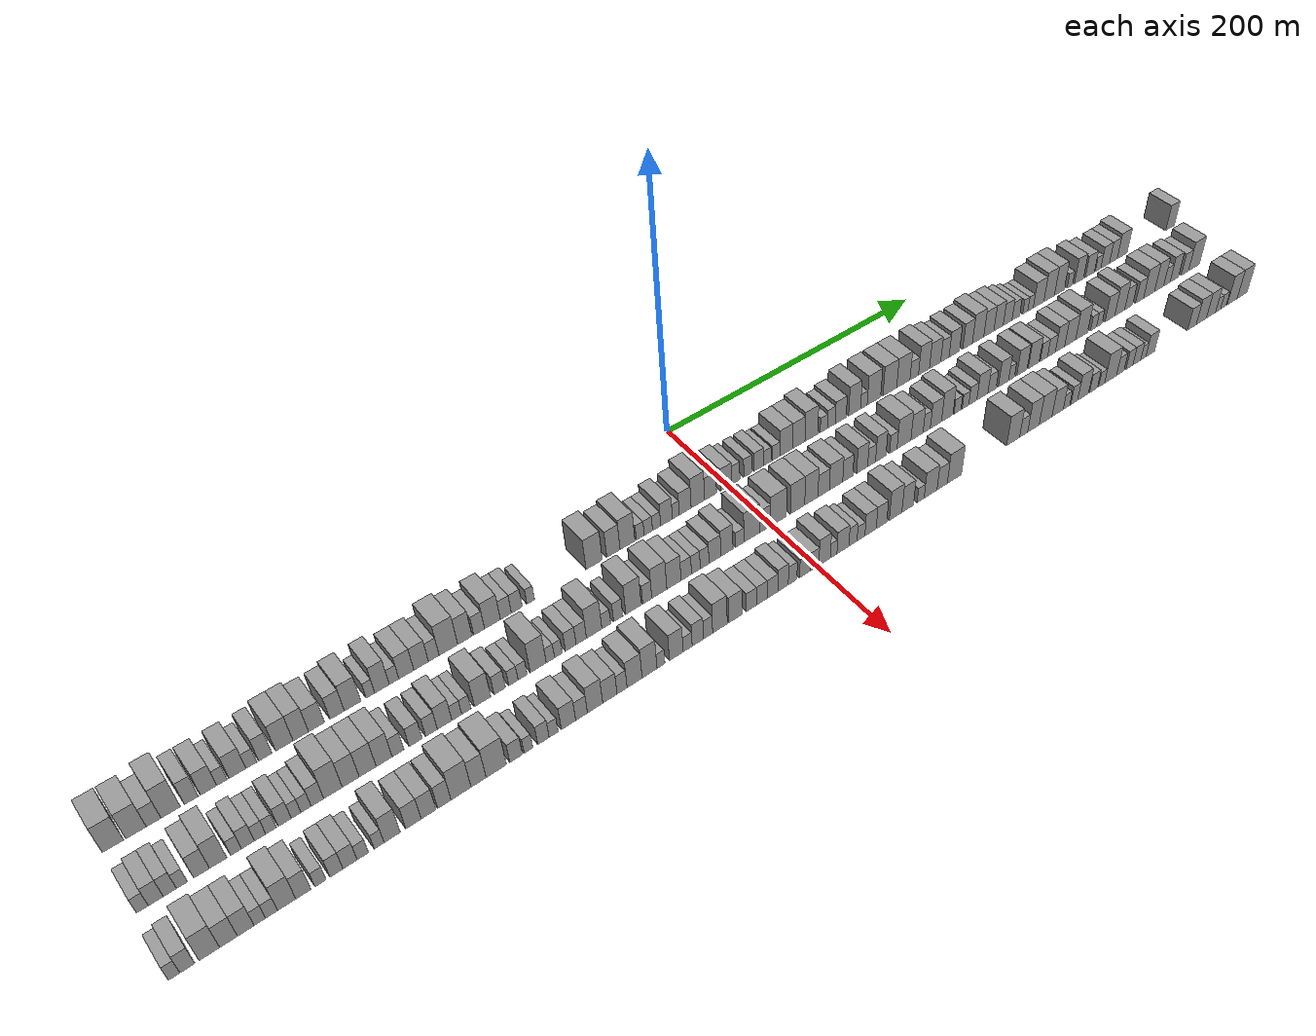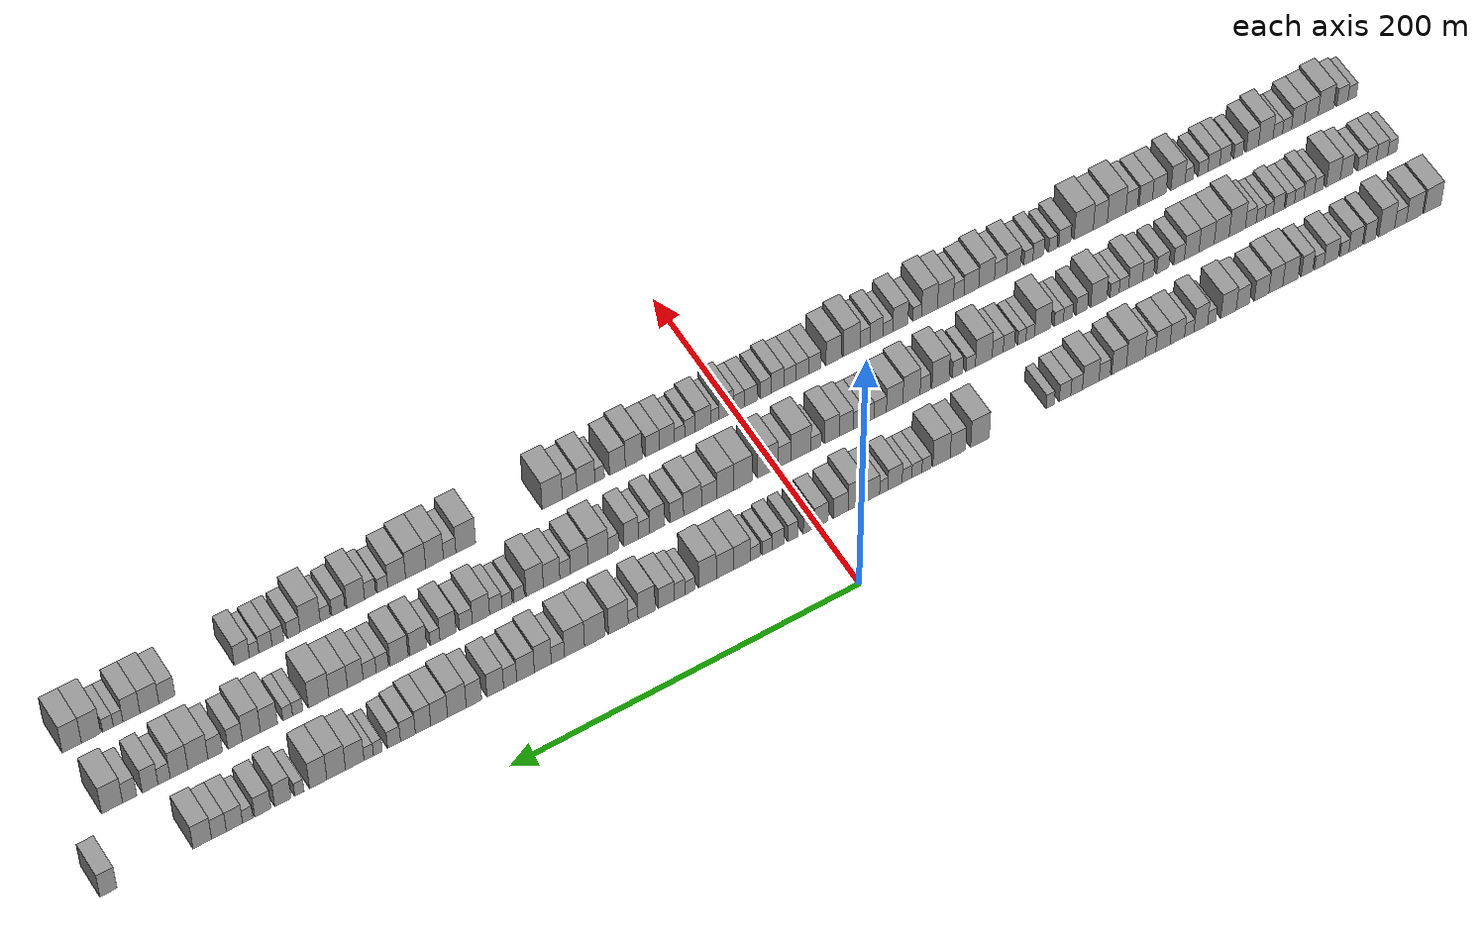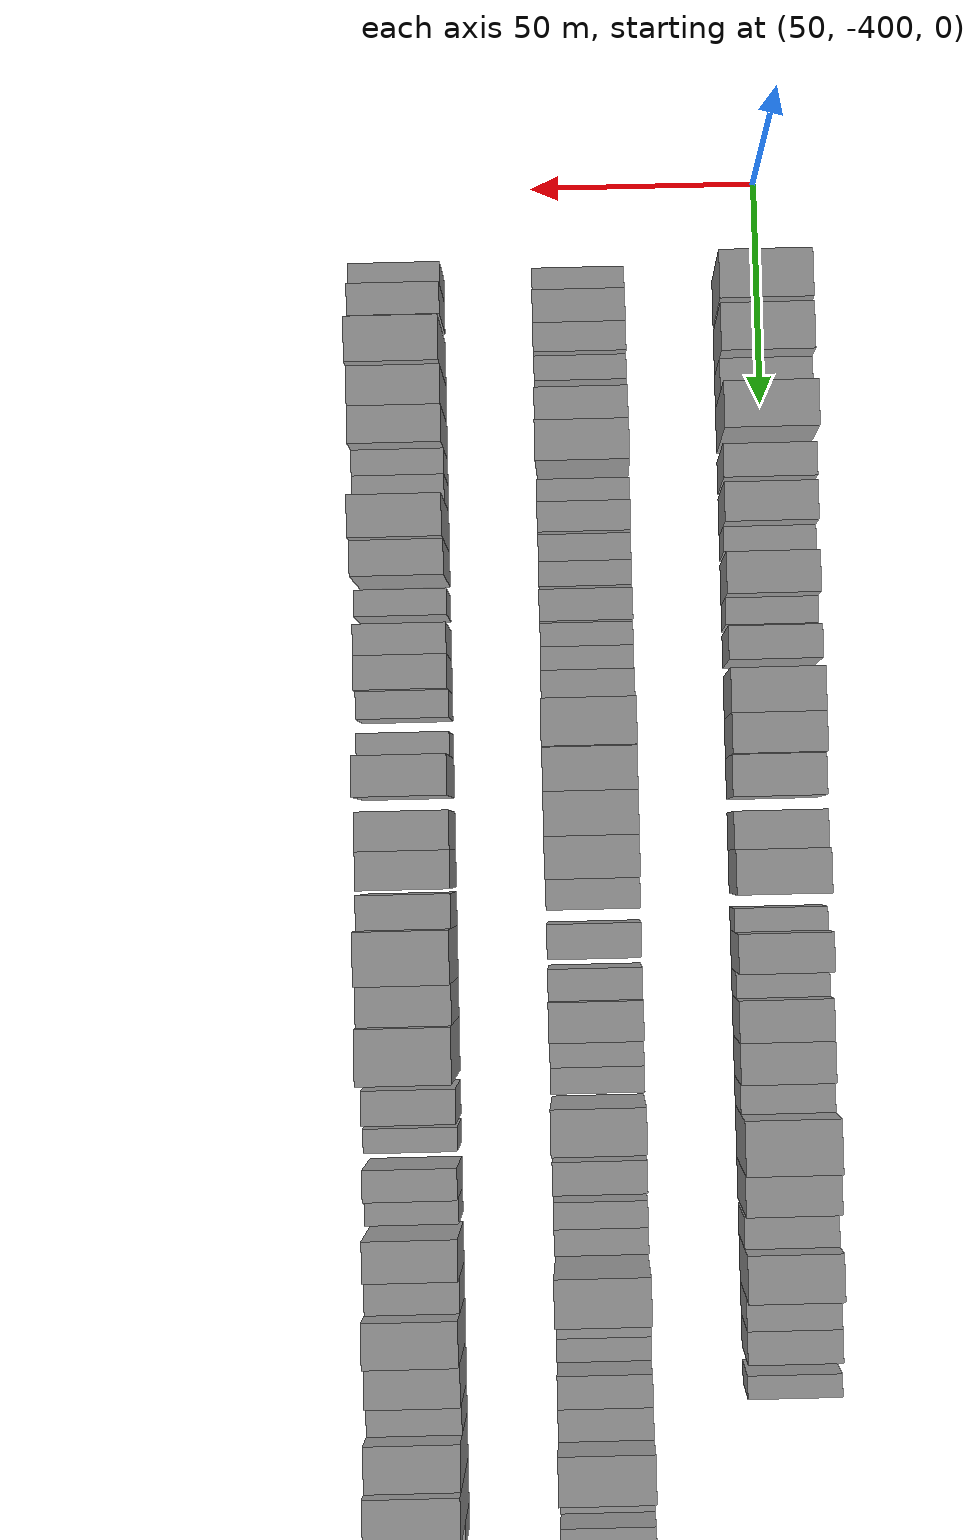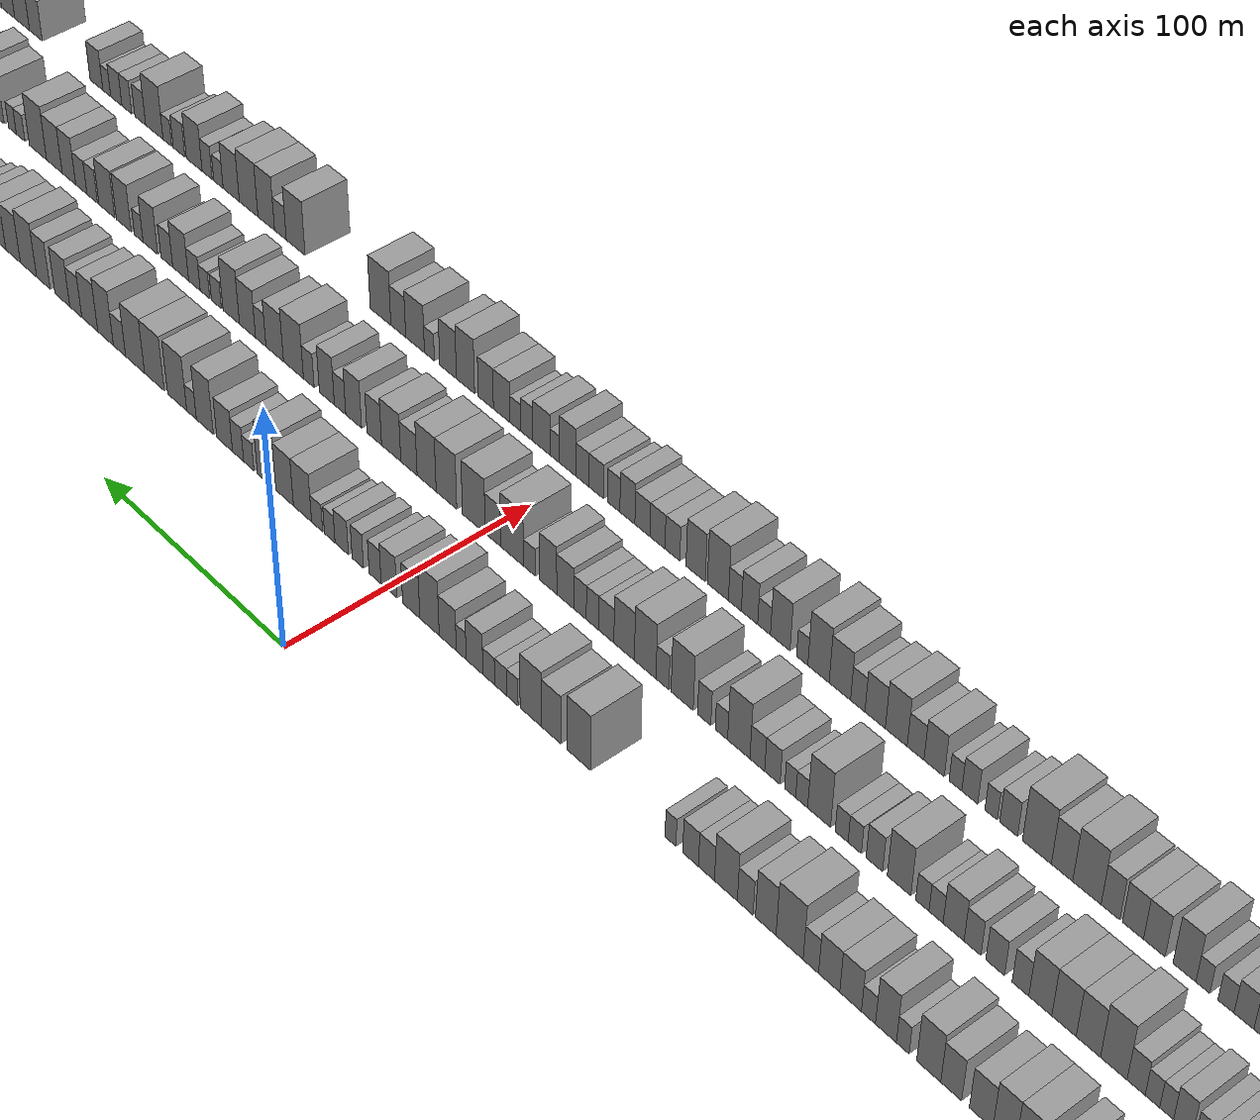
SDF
<sdf version="1.6">
 <world name="default">
  <scene>
   <sky><clouds><speed>12</speed></clouds></sky>
   <ambient>0.4 0.4 0.4 1</ambient>
   <background>0.7 0.7 0.7 1</background>
   <shadows>1</shadows>
  </scene>
  <gravity>0 0 -9.8066</gravity>
  <magnetic_field>6e-06 2.3e-05 -4.2e-05</magnetic_field>
  <physics default="0" name="default_physics" type="ode">
   <ode>
    <solver>
     <type>quick</type>
     <iters>10</iters>
     <sor>1.0</sor>
     <use_dynamic_moi_rescaling>0</use_dynamic_moi_rescaling>
    </solver>
    <constraints>
     <cfm>0</cfm>
     <erp>0.2</erp>
     <contact_max_correcting_vel>100</contact_max_correcting_vel>
     <contact_surface_layer>0.001</contact_surface_layer>
    </constraints>
   </ode>
   <max_step_size>0.004</max_step_size>
   <real_time_factor>1</real_time_factor>
   <real_time_update_rate>250</real_time_update_rate>
  </physics>
  <light name="sun" type="directional">
   <pose>0 0 10 0 0 0</pose>
   <diffuse>0.8 0.8 0.8 1</diffuse>
   <specular>0.2 0.2 0.2 1</specular>
   <attenuation>
    <range>1000</range>
    <constant>0.9</constant>
    <linear>0.01</linear>
    <quadratic>0.001</quadratic>
   </attenuation>
   <direction>-0.5 0.1 -0.9</direction>
  </light>
  <model name="building_1">
   <static>1</static>
   <pose>50.0000 -372.7563 0 0.000000 0.000000 0.000000</pose>
   <link name="link">
    <pose>0 0 10.50 0 0 0</pose>
    <collision name="collision"><geometry><box><size>20.0000 10.4874 21.0000</size></box></geometry></collision>
    <visual name="visual">
     <cast_shadows>0</cast_shadows>
     <geometry><box><size>20.0000 10.4874 21.0000</size></box></geometry>
     <material>
      <script>
       <uri>model://grey_wall/materials/scripts</uri>
       <uri>model://grey_wall/materials/textures</uri>
       <name>vrc/grey_wall</name>
      </script>
     </material>
    </visual>
   </link>
  </model>
  <model name="building_2">
   <static>1</static>
   <pose>50.0000 -361.4085 0 0.000000 0.000000 0.000000</pose>
   <link name="link">
    <pose>0 0 10.50 0 0 0</pose>
    <collision name="collision"><geometry><box><size>20.0000 10.2082 21.0000</size></box></geometry></collision>
    <visual name="visual">
     <cast_shadows>0</cast_shadows>
     <geometry><box><size>20.0000 10.2082 21.0000</size></box></geometry>
     <material>
      <script>
       <uri>model://grey_wall/materials/scripts</uri>
       <uri>model://grey_wall/materials/textures</uri>
       <name>vrc/grey_wall</name>
      </script>
     </material>
    </visual>
   </link>
  </model>
  <model name="building_3">
   <static>1</static>
   <pose>50.0000 -352.6265 0 0.000000 0.000000 0.000000</pose>
   <link name="link">
    <pose>0 0 7.50 0 0 0</pose>
    <collision name="collision"><geometry><box><size>20.0000 7.3559 15.0000</size></box></geometry></collision>
    <visual name="visual">
     <cast_shadows>0</cast_shadows>
     <geometry><box><size>20.0000 7.3559 15.0000</size></box></geometry>
     <material>
      <script>
       <uri>model://grey_wall/materials/scripts</uri>
       <uri>model://grey_wall/materials/textures</uri>
       <name>vrc/grey_wall</name>
      </script>
     </material>
    </visual>
   </link>
  </model>
  <model name="building_4">
   <static>1</static>
   <pose>50.0000 -344.0010 0 0.000000 0.000000 0.000000</pose>
   <link name="link">
    <pose>0 0 12.00 0 0 0</pose>
    <collision name="collision"><geometry><box><size>20.0000 9.8949 24.0000</size></box></geometry></collision>
    <visual name="visual">
     <cast_shadows>0</cast_shadows>
     <geometry><box><size>20.0000 9.8949 24.0000</size></box></geometry>
     <material>
      <script>
       <uri>model://grey_wall/materials/scripts</uri>
       <uri>model://grey_wall/materials/textures</uri>
       <name>vrc/grey_wall</name>
      </script>
     </material>
    </visual>
   </link>
  </model>
  <model name="building_5">
   <static>1</static>
   <pose>50.0000 -333.4457 0 0.000000 0.000000 0.000000</pose>
   <link name="link">
    <pose>0 0 9.00 0 0 0</pose>
    <collision name="collision"><geometry><box><size>20.0000 7.2157 18.0000</size></box></geometry></collision>
    <visual name="visual">
     <cast_shadows>0</cast_shadows>
     <geometry><box><size>20.0000 7.2157 18.0000</size></box></geometry>
     <material>
      <script>
       <uri>model://grey_wall/materials/scripts</uri>
       <uri>model://grey_wall/materials/textures</uri>
       <name>vrc/grey_wall</name>
      </script>
     </material>
    </visual>
   </link>
  </model>
  <model name="building_6">
   <static>1</static>
   <pose>50.0000 -324.6059 0 0.000000 0.000000 0.000000</pose>
   <link name="link">
    <pose>0 0 9.00 0 0 0</pose>
    <collision name="collision"><geometry><box><size>20.0000 8.4640 18.0000</size></box></geometry></collision>
    <visual name="visual">
     <cast_shadows>0</cast_shadows>
     <geometry><box><size>20.0000 8.4640 18.0000</size></box></geometry>
     <material>
      <script>
       <uri>model://grey_wall/materials/scripts</uri>
       <uri>model://grey_wall/materials/textures</uri>
       <name>vrc/grey_wall</name>
      </script>
     </material>
    </visual>
   </link>
  </model>
  <model name="building_7">
   <static>1</static>
   <pose>50.0000 -317.6455 0 0.000000 0.000000 0.000000</pose>
   <link name="link">
    <pose>0 0 6.00 0 0 0</pose>
    <collision name="collision"><geometry><box><size>20.0000 5.4569 12.0000</size></box></geometry></collision>
    <visual name="visual">
     <cast_shadows>0</cast_shadows>
     <geometry><box><size>20.0000 5.4569 12.0000</size></box></geometry>
     <material>
      <script>
       <uri>model://grey_wall/materials/scripts</uri>
       <uri>model://grey_wall/materials/textures</uri>
       <name>vrc/grey_wall</name>
      </script>
     </material>
    </visual>
   </link>
  </model>
  <model name="building_8">
   <static>1</static>
   <pose>50.0000 -309.4200 0 0.000000 0.000000 0.000000</pose>
   <link name="link">
    <pose>0 0 9.00 0 0 0</pose>
    <collision name="collision"><geometry><box><size>20.0000 8.9942 18.0000</size></box></geometry></collision>
    <visual name="visual">
     <cast_shadows>0</cast_shadows>
     <geometry><box><size>20.0000 8.9942 18.0000</size></box></geometry>
     <material>
      <script>
       <uri>model://grey_wall/materials/scripts</uri>
       <uri>model://grey_wall/materials/textures</uri>
       <name>vrc/grey_wall</name>
      </script>
     </material>
    </visual>
   </link>
  </model>
  <model name="building_9">
   <static>1</static>
   <pose>50.0000 -301.9996 0 0.000000 0.000000 0.000000</pose>
   <link name="link">
    <pose>0 0 6.00 0 0 0</pose>
    <collision name="collision"><geometry><box><size>20.0000 5.8465 12.0000</size></box></geometry></collision>
    <visual name="visual">
     <cast_shadows>0</cast_shadows>
     <geometry><box><size>20.0000 5.8465 12.0000</size></box></geometry>
     <material>
      <script>
       <uri>model://grey_wall/materials/scripts</uri>
       <uri>model://grey_wall/materials/textures</uri>
       <name>vrc/grey_wall</name>
      </script>
     </material>
    </visual>
   </link>
  </model>
  <model name="building_10">
   <static>1</static>
   <pose>50.0000 -294.4724 0 0.000000 0.000000 0.000000</pose>
   <link name="link">
    <pose>0 0 9.00 0 0 0</pose>
    <collision name="collision"><geometry><box><size>20.0000 7.2080 18.0000</size></box></geometry></collision>
    <visual name="visual">
     <cast_shadows>0</cast_shadows>
     <geometry><box><size>20.0000 7.2080 18.0000</size></box></geometry>
     <material>
      <script>
       <uri>model://grey_wall/materials/scripts</uri>
       <uri>model://grey_wall/materials/textures</uri>
       <name>vrc/grey_wall</name>
      </script>
     </material>
    </visual>
   </link>
  </model>
  <model name="building_11">
   <static>1</static>
   <pose>50.0000 -284.1253 0 0.000000 0.000000 0.000000</pose>
   <link name="link">
    <pose>0 0 10.50 0 0 0</pose>
    <collision name="collision"><geometry><box><size>20.0000 9.4863 21.0000</size></box></geometry></collision>
    <visual name="visual">
     <cast_shadows>0</cast_shadows>
     <geometry><box><size>20.0000 9.4863 21.0000</size></box></geometry>
     <material>
      <script>
       <uri>model://grey_wall/materials/scripts</uri>
       <uri>model://grey_wall/materials/textures</uri>
       <name>vrc/grey_wall</name>
      </script>
     </material>
    </visual>
   </link>
  </model>
  <model name="building_12">
   <static>1</static>
   <pose>50.0000 -275.1060 0 0.000000 0.000000 0.000000</pose>
   <link name="link">
    <pose>0 0 10.50 0 0 0</pose>
    <collision name="collision"><geometry><box><size>20.0000 8.5523 21.0000</size></box></geometry></collision>
    <visual name="visual">
     <cast_shadows>0</cast_shadows>
     <geometry><box><size>20.0000 8.5523 21.0000</size></box></geometry>
     <material>
      <script>
       <uri>model://grey_wall/materials/scripts</uri>
       <uri>model://grey_wall/materials/textures</uri>
       <name>vrc/grey_wall</name>
      </script>
     </material>
    </visual>
   </link>
  </model>
  <model name="building_13">
   <static>1</static>
   <pose>50.0000 -266.3483 0 0.000000 0.000000 0.000000</pose>
   <link name="link">
    <pose>0 0 9.00 0 0 0</pose>
    <collision name="collision"><geometry><box><size>20.0000 8.9630 18.0000</size></box></geometry></collision>
    <visual name="visual">
     <cast_shadows>0</cast_shadows>
     <geometry><box><size>20.0000 8.9630 18.0000</size></box></geometry>
     <material>
      <script>
       <uri>model://grey_wall/materials/scripts</uri>
       <uri>model://grey_wall/materials/textures</uri>
       <name>vrc/grey_wall</name>
      </script>
     </material>
    </visual>
   </link>
  </model>
  <model name="building_14">
   <static>1</static>
   <pose>50.0000 -254.8065 0 0.000000 0.000000 0.000000</pose>
   <link name="link">
    <pose>0 0 9.00 0 0 0</pose>
    <collision name="collision"><geometry><box><size>20.0000 8.1206 18.0000</size></box></geometry></collision>
    <visual name="visual">
     <cast_shadows>0</cast_shadows>
     <geometry><box><size>20.0000 8.1206 18.0000</size></box></geometry>
     <material>
      <script>
       <uri>model://grey_wall/materials/scripts</uri>
       <uri>model://grey_wall/materials/textures</uri>
       <name>vrc/grey_wall</name>
      </script>
     </material>
    </visual>
   </link>
  </model>
  <model name="building_15">
   <static>1</static>
   <pose>50.0000 -246.0079 0 0.000000 0.000000 0.000000</pose>
   <link name="link">
    <pose>0 0 10.50 0 0 0</pose>
    <collision name="collision"><geometry><box><size>20.0000 9.4766 21.0000</size></box></geometry></collision>
    <visual name="visual">
     <cast_shadows>0</cast_shadows>
     <geometry><box><size>20.0000 9.4766 21.0000</size></box></geometry>
     <material>
      <script>
       <uri>model://grey_wall/materials/scripts</uri>
       <uri>model://grey_wall/materials/textures</uri>
       <name>vrc/grey_wall</name>
      </script>
     </material>
    </visual>
   </link>
  </model>
  <model name="building_16">
   <static>1</static>
   <pose>50.0000 -235.7292 0 0.000000 0.000000 0.000000</pose>
   <link name="link">
    <pose>0 0 6.00 0 0 0</pose>
    <collision name="collision"><geometry><box><size>20.0000 5.0809 12.0000</size></box></geometry></collision>
    <visual name="visual">
     <cast_shadows>0</cast_shadows>
     <geometry><box><size>20.0000 5.0809 12.0000</size></box></geometry>
     <material>
      <script>
       <uri>model://grey_wall/materials/scripts</uri>
       <uri>model://grey_wall/materials/textures</uri>
       <name>vrc/grey_wall</name>
      </script>
     </material>
    </visual>
   </link>
  </model>
  <model name="building_17">
   <static>1</static>
   <pose>50.0000 -228.9872 0 0.000000 0.000000 0.000000</pose>
   <link name="link">
    <pose>0 0 10.50 0 0 0</pose>
    <collision name="collision"><geometry><box><size>20.0000 8.4031 21.0000</size></box></geometry></collision>
    <visual name="visual">
     <cast_shadows>0</cast_shadows>
     <geometry><box><size>20.0000 8.4031 21.0000</size></box></geometry>
     <material>
      <script>
       <uri>model://grey_wall/materials/scripts</uri>
       <uri>model://grey_wall/materials/textures</uri>
       <name>vrc/grey_wall</name>
      </script>
     </material>
    </visual>
   </link>
  </model>
  <model name="building_18">
   <static>1</static>
   <pose>50.0000 -221.9549 0 0.000000 0.000000 0.000000</pose>
   <link name="link">
    <pose>0 0 6.00 0 0 0</pose>
    <collision name="collision"><geometry><box><size>20.0000 5.6615 12.0000</size></box></geometry></collision>
    <visual name="visual">
     <cast_shadows>0</cast_shadows>
     <geometry><box><size>20.0000 5.6615 12.0000</size></box></geometry>
     <material>
      <script>
       <uri>model://grey_wall/materials/scripts</uri>
       <uri>model://grey_wall/materials/textures</uri>
       <name>vrc/grey_wall</name>
      </script>
     </material>
    </visual>
   </link>
  </model>
  <model name="building_19">
   <static>1</static>
   <pose>50.0000 -214.6884 0 0.000000 0.000000 0.000000</pose>
   <link name="link">
    <pose>0 0 9.00 0 0 0</pose>
    <collision name="collision"><geometry><box><size>20.0000 8.8716 18.0000</size></box></geometry></collision>
    <visual name="visual">
     <cast_shadows>0</cast_shadows>
     <geometry><box><size>20.0000 8.8716 18.0000</size></box></geometry>
     <material>
      <script>
       <uri>model://grey_wall/materials/scripts</uri>
       <uri>model://grey_wall/materials/textures</uri>
       <name>vrc/grey_wall</name>
      </script>
     </material>
    </visual>
   </link>
  </model>
  <model name="building_20">
   <static>1</static>
   <pose>50.0000 -205.8863 0 0.000000 0.000000 0.000000</pose>
   <link name="link">
    <pose>0 0 9.00 0 0 0</pose>
    <collision name="collision"><geometry><box><size>20.0000 8.7325 18.0000</size></box></geometry></collision>
    <visual name="visual">
     <cast_shadows>0</cast_shadows>
     <geometry><box><size>20.0000 8.7325 18.0000</size></box></geometry>
     <material>
      <script>
       <uri>model://grey_wall/materials/scripts</uri>
       <uri>model://grey_wall/materials/textures</uri>
       <name>vrc/grey_wall</name>
      </script>
     </material>
    </visual>
   </link>
  </model>
  <model name="building_21">
   <static>1</static>
   <pose>50.0000 -198.3036 0 0.000000 0.000000 0.000000</pose>
   <link name="link">
    <pose>0 0 7.50 0 0 0</pose>
    <collision name="collision"><geometry><box><size>20.0000 6.4328 15.0000</size></box></geometry></collision>
    <visual name="visual">
     <cast_shadows>0</cast_shadows>
     <geometry><box><size>20.0000 6.4328 15.0000</size></box></geometry>
     <material>
      <script>
       <uri>model://grey_wall/materials/scripts</uri>
       <uri>model://grey_wall/materials/textures</uri>
       <name>vrc/grey_wall</name>
      </script>
     </material>
    </visual>
   </link>
  </model>
  <model name="building_22">
   <static>1</static>
   <pose>50.0000 -189.3780 0 0.000000 0.000000 0.000000</pose>
   <link name="link">
    <pose>0 0 12.00 0 0 0</pose>
    <collision name="collision"><geometry><box><size>20.0000 11.4183 24.0000</size></box></geometry></collision>
    <visual name="visual">
     <cast_shadows>0</cast_shadows>
     <geometry><box><size>20.0000 11.4183 24.0000</size></box></geometry>
     <material>
      <script>
       <uri>model://grey_wall/materials/scripts</uri>
       <uri>model://grey_wall/materials/textures</uri>
       <name>vrc/grey_wall</name>
      </script>
     </material>
    </visual>
   </link>
  </model>
  <model name="building_23">
   <static>1</static>
   <pose>50.0000 -179.2558 0 0.000000 0.000000 0.000000</pose>
   <link name="link">
    <pose>0 0 10.50 0 0 0</pose>
    <collision name="collision"><geometry><box><size>20.0000 8.8261 21.0000</size></box></geometry></collision>
    <visual name="visual">
     <cast_shadows>0</cast_shadows>
     <geometry><box><size>20.0000 8.8261 21.0000</size></box></geometry>
     <material>
      <script>
       <uri>model://grey_wall/materials/scripts</uri>
       <uri>model://grey_wall/materials/textures</uri>
       <name>vrc/grey_wall</name>
      </script>
     </material>
    </visual>
   </link>
  </model>
  <model name="building_24">
   <static>1</static>
   <pose>50.0000 -170.4617 0 0.000000 0.000000 0.000000</pose>
   <link name="link">
    <pose>0 0 7.50 0 0 0</pose>
    <collision name="collision"><geometry><box><size>20.0000 6.7623 15.0000</size></box></geometry></collision>
    <visual name="visual">
     <cast_shadows>0</cast_shadows>
     <geometry><box><size>20.0000 6.7623 15.0000</size></box></geometry>
     <material>
      <script>
       <uri>model://grey_wall/materials/scripts</uri>
       <uri>model://grey_wall/materials/textures</uri>
       <name>vrc/grey_wall</name>
      </script>
     </material>
    </visual>
   </link>
  </model>
  <model name="building_25">
   <static>1</static>
   <pose>50.0000 -162.0991 0 0.000000 0.000000 0.000000</pose>
   <link name="link">
    <pose>0 0 10.50 0 0 0</pose>
    <collision name="collision"><geometry><box><size>20.0000 9.9630 21.0000</size></box></geometry></collision>
    <visual name="visual">
     <cast_shadows>0</cast_shadows>
     <geometry><box><size>20.0000 9.9630 21.0000</size></box></geometry>
     <material>
      <script>
       <uri>model://grey_wall/materials/scripts</uri>
       <uri>model://grey_wall/materials/textures</uri>
       <name>vrc/grey_wall</name>
      </script>
     </material>
    </visual>
   </link>
  </model>
  <model name="building_26">
   <static>1</static>
   <pose>50.0000 -153.5990 0 0.000000 0.000000 0.000000</pose>
   <link name="link">
    <pose>0 0 7.50 0 0 0</pose>
    <collision name="collision"><geometry><box><size>20.0000 7.0372 15.0000</size></box></geometry></collision>
    <visual name="visual">
     <cast_shadows>0</cast_shadows>
     <geometry><box><size>20.0000 7.0372 15.0000</size></box></geometry>
     <material>
      <script>
       <uri>model://grey_wall/materials/scripts</uri>
       <uri>model://grey_wall/materials/textures</uri>
       <name>vrc/grey_wall</name>
      </script>
     </material>
    </visual>
   </link>
  </model>
  <model name="building_27">
   <static>1</static>
   <pose>50.0000 -146.6051 0 0.000000 0.000000 0.000000</pose>
   <link name="link">
    <pose>0 0 7.50 0 0 0</pose>
    <collision name="collision"><geometry><box><size>20.0000 6.9507 15.0000</size></box></geometry></collision>
    <visual name="visual">
     <cast_shadows>0</cast_shadows>
     <geometry><box><size>20.0000 6.9507 15.0000</size></box></geometry>
     <material>
      <script>
       <uri>model://grey_wall/materials/scripts</uri>
       <uri>model://grey_wall/materials/textures</uri>
       <name>vrc/grey_wall</name>
      </script>
     </material>
    </visual>
   </link>
  </model>
  <model name="building_28">
   <static>1</static>
   <pose>50.0000 -137.6963 0 0.000000 0.000000 0.000000</pose>
   <link name="link">
    <pose>0 0 6.00 0 0 0</pose>
    <collision name="collision"><geometry><box><size>20.0000 4.8668 12.0000</size></box></geometry></collision>
    <visual name="visual">
     <cast_shadows>0</cast_shadows>
     <geometry><box><size>20.0000 4.8668 12.0000</size></box></geometry>
     <material>
      <script>
       <uri>model://grey_wall/materials/scripts</uri>
       <uri>model://grey_wall/materials/textures</uri>
       <name>vrc/grey_wall</name>
      </script>
     </material>
    </visual>
   </link>
  </model>
  <model name="building_29">
   <static>1</static>
   <pose>50.0000 -95.6276 0 0.000000 0.000000 0.000000</pose>
   <link name="link">
    <pose>0 0 12.00 0 0 0</pose>
    <collision name="collision"><geometry><box><size>20.0000 11.0902 24.0000</size></box></geometry></collision>
    <visual name="visual">
     <cast_shadows>0</cast_shadows>
     <geometry><box><size>20.0000 11.0902 24.0000</size></box></geometry>
     <material>
      <script>
       <uri>model://grey_wall/materials/scripts</uri>
       <uri>model://grey_wall/materials/textures</uri>
       <name>vrc/grey_wall</name>
      </script>
     </material>
    </visual>
   </link>
  </model>
  <model name="building_30">
   <static>1</static>
   <pose>50.0000 -82.5195 0 0.000000 0.000000 0.000000</pose>
   <link name="link">
    <pose>0 0 10.50 0 0 0</pose>
    <collision name="collision"><geometry><box><size>20.0000 9.1260 21.0000</size></box></geometry></collision>
    <visual name="visual">
     <cast_shadows>0</cast_shadows>
     <geometry><box><size>20.0000 9.1260 21.0000</size></box></geometry>
     <material>
      <script>
       <uri>model://grey_wall/materials/scripts</uri>
       <uri>model://grey_wall/materials/textures</uri>
       <name>vrc/grey_wall</name>
      </script>
     </material>
    </visual>
   </link>
  </model>
  <model name="building_31">
   <static>1</static>
   <pose>50.0000 -72.8007 0 0.000000 0.000000 0.000000</pose>
   <link name="link">
    <pose>0 0 12.00 0 0 0</pose>
    <collision name="collision"><geometry><box><size>20.0000 10.3116 24.0000</size></box></geometry></collision>
    <visual name="visual">
     <cast_shadows>0</cast_shadows>
     <geometry><box><size>20.0000 10.3116 24.0000</size></box></geometry>
     <material>
      <script>
       <uri>model://grey_wall/materials/scripts</uri>
       <uri>model://grey_wall/materials/textures</uri>
       <name>vrc/grey_wall</name>
      </script>
     </material>
    </visual>
   </link>
  </model>
  <model name="building_32">
   <static>1</static>
   <pose>50.0000 -63.9002 0 0.000000 0.000000 0.000000</pose>
   <link name="link">
    <pose>0 0 6.00 0 0 0</pose>
    <collision name="collision"><geometry><box><size>20.0000 5.4893 12.0000</size></box></geometry></collision>
    <visual name="visual">
     <cast_shadows>0</cast_shadows>
     <geometry><box><size>20.0000 5.4893 12.0000</size></box></geometry>
     <material>
      <script>
       <uri>model://grey_wall/materials/scripts</uri>
       <uri>model://grey_wall/materials/textures</uri>
       <name>vrc/grey_wall</name>
      </script>
     </material>
    </visual>
   </link>
  </model>
  <model name="building_33">
   <static>1</static>
   <pose>50.0000 -58.2118 0 0.000000 0.000000 0.000000</pose>
   <link name="link">
    <pose>0 0 6.00 0 0 0</pose>
    <collision name="collision"><geometry><box><size>20.0000 5.8876 12.0000</size></box></geometry></collision>
    <visual name="visual">
     <cast_shadows>0</cast_shadows>
     <geometry><box><size>20.0000 5.8876 12.0000</size></box></geometry>
     <material>
      <script>
       <uri>model://grey_wall/materials/scripts</uri>
       <uri>model://grey_wall/materials/textures</uri>
       <name>vrc/grey_wall</name>
      </script>
     </material>
    </visual>
   </link>
  </model>
  <model name="building_34">
   <static>1</static>
   <pose>50.0000 -52.3605 0 0.000000 0.000000 0.000000</pose>
   <link name="link">
    <pose>0 0 6.00 0 0 0</pose>
    <collision name="collision"><geometry><box><size>20.0000 5.8150 12.0000</size></box></geometry></collision>
    <visual name="visual">
     <cast_shadows>0</cast_shadows>
     <geometry><box><size>20.0000 5.8150 12.0000</size></box></geometry>
     <material>
      <script>
       <uri>model://grey_wall/materials/scripts</uri>
       <uri>model://grey_wall/materials/textures</uri>
       <name>vrc/grey_wall</name>
      </script>
     </material>
    </visual>
   </link>
  </model>
  <model name="building_35">
   <static>1</static>
   <pose>50.0000 -45.2848 0 0.000000 0.000000 0.000000</pose>
   <link name="link">
    <pose>0 0 9.00 0 0 0</pose>
    <collision name="collision"><geometry><box><size>20.0000 8.3363 18.0000</size></box></geometry></collision>
    <visual name="visual">
     <cast_shadows>0</cast_shadows>
     <geometry><box><size>20.0000 8.3363 18.0000</size></box></geometry>
     <material>
      <script>
       <uri>model://grey_wall/materials/scripts</uri>
       <uri>model://grey_wall/materials/textures</uri>
       <name>vrc/grey_wall</name>
      </script>
     </material>
    </visual>
   </link>
  </model>
  <model name="building_36">
   <static>1</static>
   <pose>50.0000 -38.6339 0 0.000000 0.000000 0.000000</pose>
   <link name="link">
    <pose>0 0 6.00 0 0 0</pose>
    <collision name="collision"><geometry><box><size>20.0000 4.9655 12.0000</size></box></geometry></collision>
    <visual name="visual">
     <cast_shadows>0</cast_shadows>
     <geometry><box><size>20.0000 4.9655 12.0000</size></box></geometry>
     <material>
      <script>
       <uri>model://grey_wall/materials/scripts</uri>
       <uri>model://grey_wall/materials/textures</uri>
       <name>vrc/grey_wall</name>
      </script>
     </material>
    </visual>
   </link>
  </model>
  <model name="building_37">
   <static>1</static>
   <pose>50.0000 -31.8474 0 0.000000 0.000000 0.000000</pose>
   <link name="link">
    <pose>0 0 9.00 0 0 0</pose>
    <collision name="collision"><geometry><box><size>20.0000 8.6075 18.0000</size></box></geometry></collision>
    <visual name="visual">
     <cast_shadows>0</cast_shadows>
     <geometry><box><size>20.0000 8.6075 18.0000</size></box></geometry>
     <material>
      <script>
       <uri>model://grey_wall/materials/scripts</uri>
       <uri>model://grey_wall/materials/textures</uri>
       <name>vrc/grey_wall</name>
      </script>
     </material>
    </visual>
   </link>
  </model>
  <model name="building_38">
   <static>1</static>
   <pose>50.0000 -22.6203 0 0.000000 0.000000 0.000000</pose>
   <link name="link">
    <pose>0 0 12.00 0 0 0</pose>
    <collision name="collision"><geometry><box><size>20.0000 9.8466 24.0000</size></box></geometry></collision>
    <visual name="visual">
     <cast_shadows>0</cast_shadows>
     <geometry><box><size>20.0000 9.8466 24.0000</size></box></geometry>
     <material>
      <script>
       <uri>model://grey_wall/materials/scripts</uri>
       <uri>model://grey_wall/materials/textures</uri>
       <name>vrc/grey_wall</name>
      </script>
     </material>
    </visual>
   </link>
  </model>
  <model name="building_39">
   <static>1</static>
   <pose>50.0000 -13.2915 0 0.000000 0.000000 0.000000</pose>
   <link name="link">
    <pose>0 0 9.00 0 0 0</pose>
    <collision name="collision"><geometry><box><size>20.0000 8.8109 18.0000</size></box></geometry></collision>
    <visual name="visual">
     <cast_shadows>0</cast_shadows>
     <geometry><box><size>20.0000 8.8109 18.0000</size></box></geometry>
     <material>
      <script>
       <uri>model://grey_wall/materials/scripts</uri>
       <uri>model://grey_wall/materials/textures</uri>
       <name>vrc/grey_wall</name>
      </script>
     </material>
    </visual>
   </link>
  </model>
  <model name="building_40">
   <static>1</static>
   <pose>50.0000 -1.7778 0 0.000000 0.000000 0.000000</pose>
   <link name="link">
    <pose>0 0 9.00 0 0 0</pose>
    <collision name="collision"><geometry><box><size>20.0000 8.2166 18.0000</size></box></geometry></collision>
    <visual name="visual">
     <cast_shadows>0</cast_shadows>
     <geometry><box><size>20.0000 8.2166 18.0000</size></box></geometry>
     <material>
      <script>
       <uri>model://grey_wall/materials/scripts</uri>
       <uri>model://grey_wall/materials/textures</uri>
       <name>vrc/grey_wall</name>
      </script>
     </material>
    </visual>
   </link>
  </model>
  <model name="building_41">
   <static>1</static>
   <pose>50.0000 5.4653 0 0.000000 0.000000 0.000000</pose>
   <link name="link">
    <pose>0 0 7.50 0 0 0</pose>
    <collision name="collision"><geometry><box><size>20.0000 6.2696 15.0000</size></box></geometry></collision>
    <visual name="visual">
     <cast_shadows>0</cast_shadows>
     <geometry><box><size>20.0000 6.2696 15.0000</size></box></geometry>
     <material>
      <script>
       <uri>model://grey_wall/materials/scripts</uri>
       <uri>model://grey_wall/materials/textures</uri>
       <name>vrc/grey_wall</name>
      </script>
     </material>
    </visual>
   </link>
  </model>
  <model name="building_42">
   <static>1</static>
   <pose>50.0000 14.6106 0 0.000000 0.000000 0.000000</pose>
   <link name="link">
    <pose>0 0 7.50 0 0 0</pose>
    <collision name="collision"><geometry><box><size>20.0000 6.0210 15.0000</size></box></geometry></collision>
    <visual name="visual">
     <cast_shadows>0</cast_shadows>
     <geometry><box><size>20.0000 6.0210 15.0000</size></box></geometry>
     <material>
      <script>
       <uri>model://grey_wall/materials/scripts</uri>
       <uri>model://grey_wall/materials/textures</uri>
       <name>vrc/grey_wall</name>
      </script>
     </material>
    </visual>
   </link>
  </model>
  <model name="building_43">
   <static>1</static>
   <pose>50.0000 23.2075 0 0.000000 0.000000 0.000000</pose>
   <link name="link">
    <pose>0 0 7.50 0 0 0</pose>
    <collision name="collision"><geometry><box><size>20.0000 7.1727 15.0000</size></box></geometry></collision>
    <visual name="visual">
     <cast_shadows>0</cast_shadows>
     <geometry><box><size>20.0000 7.1727 15.0000</size></box></geometry>
     <material>
      <script>
       <uri>model://grey_wall/materials/scripts</uri>
       <uri>model://grey_wall/materials/textures</uri>
       <name>vrc/grey_wall</name>
      </script>
     </material>
    </visual>
   </link>
  </model>
  <model name="building_44">
   <static>1</static>
   <pose>50.0000 29.6395 0 0.000000 0.000000 0.000000</pose>
   <link name="link">
    <pose>0 0 6.00 0 0 0</pose>
    <collision name="collision"><geometry><box><size>20.0000 5.6913 12.0000</size></box></geometry></collision>
    <visual name="visual">
     <cast_shadows>0</cast_shadows>
     <geometry><box><size>20.0000 5.6913 12.0000</size></box></geometry>
     <material>
      <script>
       <uri>model://grey_wall/materials/scripts</uri>
       <uri>model://grey_wall/materials/textures</uri>
       <name>vrc/grey_wall</name>
      </script>
     </material>
    </visual>
   </link>
  </model>
  <model name="building_45">
   <static>1</static>
   <pose>50.0000 36.4650 0 0.000000 0.000000 0.000000</pose>
   <link name="link">
    <pose>0 0 6.00 0 0 0</pose>
    <collision name="collision"><geometry><box><size>20.0000 5.9598 12.0000</size></box></geometry></collision>
    <visual name="visual">
     <cast_shadows>0</cast_shadows>
     <geometry><box><size>20.0000 5.9598 12.0000</size></box></geometry>
     <material>
      <script>
       <uri>model://grey_wall/materials/scripts</uri>
       <uri>model://grey_wall/materials/textures</uri>
       <name>vrc/grey_wall</name>
      </script>
     </material>
    </visual>
   </link>
  </model>
  <model name="building_46">
   <static>1</static>
   <pose>50.0000 44.4060 0 0.000000 0.000000 0.000000</pose>
   <link name="link">
    <pose>0 0 10.50 0 0 0</pose>
    <collision name="collision"><geometry><box><size>20.0000 9.9222 21.0000</size></box></geometry></collision>
    <visual name="visual">
     <cast_shadows>0</cast_shadows>
     <geometry><box><size>20.0000 9.9222 21.0000</size></box></geometry>
     <material>
      <script>
       <uri>model://grey_wall/materials/scripts</uri>
       <uri>model://grey_wall/materials/textures</uri>
       <name>vrc/grey_wall</name>
      </script>
     </material>
    </visual>
   </link>
  </model>
  <model name="building_47">
   <static>1</static>
   <pose>50.0000 54.2389 0 0.000000 0.000000 0.000000</pose>
   <link name="link">
    <pose>0 0 10.50 0 0 0</pose>
    <collision name="collision"><geometry><box><size>20.0000 9.7437 21.0000</size></box></geometry></collision>
    <visual name="visual">
     <cast_shadows>0</cast_shadows>
     <geometry><box><size>20.0000 9.7437 21.0000</size></box></geometry>
     <material>
      <script>
       <uri>model://grey_wall/materials/scripts</uri>
       <uri>model://grey_wall/materials/textures</uri>
       <name>vrc/grey_wall</name>
      </script>
     </material>
    </visual>
   </link>
  </model>
  <model name="building_48">
   <static>1</static>
   <pose>50.0000 64.2303 0 0.000000 0.000000 0.000000</pose>
   <link name="link">
    <pose>0 0 12.00 0 0 0</pose>
    <collision name="collision"><geometry><box><size>20.0000 10.2391 24.0000</size></box></geometry></collision>
    <visual name="visual">
     <cast_shadows>0</cast_shadows>
     <geometry><box><size>20.0000 10.2391 24.0000</size></box></geometry>
     <material>
      <script>
       <uri>model://grey_wall/materials/scripts</uri>
       <uri>model://grey_wall/materials/textures</uri>
       <name>vrc/grey_wall</name>
      </script>
     </material>
    </visual>
   </link>
  </model>
  <model name="building_49">
   <static>1</static>
   <pose>50.0000 74.2547 0 0.000000 0.000000 0.000000</pose>
   <link name="link">
    <pose>0 0 6.00 0 0 0</pose>
    <collision name="collision"><geometry><box><size>20.0000 5.8098 12.0000</size></box></geometry></collision>
    <visual name="visual">
     <cast_shadows>0</cast_shadows>
     <geometry><box><size>20.0000 5.8098 12.0000</size></box></geometry>
     <material>
      <script>
       <uri>model://grey_wall/materials/scripts</uri>
       <uri>model://grey_wall/materials/textures</uri>
       <name>vrc/grey_wall</name>
      </script>
     </material>
    </visual>
   </link>
  </model>
  <model name="building_50">
   <static>1</static>
   <pose>50.0000 80.3056 0 0.000000 0.000000 0.000000</pose>
   <link name="link">
    <pose>0 0 7.50 0 0 0</pose>
    <collision name="collision"><geometry><box><size>20.0000 6.2919 15.0000</size></box></geometry></collision>
    <visual name="visual">
     <cast_shadows>0</cast_shadows>
     <geometry><box><size>20.0000 6.2919 15.0000</size></box></geometry>
     <material>
      <script>
       <uri>model://grey_wall/materials/scripts</uri>
       <uri>model://grey_wall/materials/textures</uri>
       <name>vrc/grey_wall</name>
      </script>
     </material>
    </visual>
   </link>
  </model>
  <model name="building_51">
   <static>1</static>
   <pose>50.0000 87.9464 0 0.000000 0.000000 0.000000</pose>
   <link name="link">
    <pose>0 0 9.00 0 0 0</pose>
    <collision name="collision"><geometry><box><size>20.0000 8.9897 18.0000</size></box></geometry></collision>
    <visual name="visual">
     <cast_shadows>0</cast_shadows>
     <geometry><box><size>20.0000 8.9897 18.0000</size></box></geometry>
     <material>
      <script>
       <uri>model://grey_wall/materials/scripts</uri>
       <uri>model://grey_wall/materials/textures</uri>
       <name>vrc/grey_wall</name>
      </script>
     </material>
    </visual>
   </link>
  </model>
  <model name="building_52">
   <static>1</static>
   <pose>50.0000 99.3654 0 0.000000 0.000000 0.000000</pose>
   <link name="link">
    <pose>0 0 12.00 0 0 0</pose>
    <collision name="collision"><geometry><box><size>20.0000 9.8483 24.0000</size></box></geometry></collision>
    <visual name="visual">
     <cast_shadows>0</cast_shadows>
     <geometry><box><size>20.0000 9.8483 24.0000</size></box></geometry>
     <material>
      <script>
       <uri>model://grey_wall/materials/scripts</uri>
       <uri>model://grey_wall/materials/textures</uri>
       <name>vrc/grey_wall</name>
      </script>
     </material>
    </visual>
   </link>
  </model>
  <model name="building_53">
   <static>1</static>
   <pose>50.0000 107.1000 0 0.000000 0.000000 0.000000</pose>
   <link name="link">
    <pose>0 0 6.00 0 0 0</pose>
    <collision name="collision"><geometry><box><size>20.0000 5.6209 12.0000</size></box></geometry></collision>
    <visual name="visual">
     <cast_shadows>0</cast_shadows>
     <geometry><box><size>20.0000 5.6209 12.0000</size></box></geometry>
     <material>
      <script>
       <uri>model://grey_wall/materials/scripts</uri>
       <uri>model://grey_wall/materials/textures</uri>
       <name>vrc/grey_wall</name>
      </script>
     </material>
    </visual>
   </link>
  </model>
  <model name="building_54">
   <static>1</static>
   <pose>50.0000 115.5343 0 0.000000 0.000000 0.000000</pose>
   <link name="link">
    <pose>0 0 12.00 0 0 0</pose>
    <collision name="collision"><geometry><box><size>20.0000 11.2476 24.0000</size></box></geometry></collision>
    <visual name="visual">
     <cast_shadows>0</cast_shadows>
     <geometry><box><size>20.0000 11.2476 24.0000</size></box></geometry>
     <material>
      <script>
       <uri>model://grey_wall/materials/scripts</uri>
       <uri>model://grey_wall/materials/textures</uri>
       <name>vrc/grey_wall</name>
      </script>
     </material>
    </visual>
   </link>
  </model>
  <model name="building_55">
   <static>1</static>
   <pose>50.0000 129.0157 0 0.000000 0.000000 0.000000</pose>
   <link name="link">
    <pose>0 0 12.00 0 0 0</pose>
    <collision name="collision"><geometry><box><size>20.0000 11.7152 24.0000</size></box></geometry></collision>
    <visual name="visual">
     <cast_shadows>0</cast_shadows>
     <geometry><box><size>20.0000 11.7152 24.0000</size></box></geometry>
     <material>
      <script>
       <uri>model://grey_wall/materials/scripts</uri>
       <uri>model://grey_wall/materials/textures</uri>
       <name>vrc/grey_wall</name>
      </script>
     </material>
    </visual>
   </link>
  </model>
  <model name="building_56">
   <static>1</static>
   <pose>50.0000 140.5876 0 0.000000 0.000000 0.000000</pose>
   <link name="link">
    <pose>0 0 12.00 0 0 0</pose>
    <collision name="collision"><geometry><box><size>20.0000 11.4286 24.0000</size></box></geometry></collision>
    <visual name="visual">
     <cast_shadows>0</cast_shadows>
     <geometry><box><size>20.0000 11.4286 24.0000</size></box></geometry>
     <material>
      <script>
       <uri>model://grey_wall/materials/scripts</uri>
       <uri>model://grey_wall/materials/textures</uri>
       <name>vrc/grey_wall</name>
      </script>
     </material>
    </visual>
   </link>
  </model>
  <model name="building_57">
   <static>1</static>
   <pose>50.0000 150.0243 0 0.000000 0.000000 0.000000</pose>
   <link name="link">
    <pose>0 0 7.50 0 0 0</pose>
    <collision name="collision"><geometry><box><size>20.0000 7.4448 15.0000</size></box></geometry></collision>
    <visual name="visual">
     <cast_shadows>0</cast_shadows>
     <geometry><box><size>20.0000 7.4448 15.0000</size></box></geometry>
     <material>
      <script>
       <uri>model://grey_wall/materials/scripts</uri>
       <uri>model://grey_wall/materials/textures</uri>
       <name>vrc/grey_wall</name>
      </script>
     </material>
    </visual>
   </link>
  </model>
  <model name="building_58">
   <static>1</static>
   <pose>50.0000 158.5561 0 0.000000 0.000000 0.000000</pose>
   <link name="link">
    <pose>0 0 12.00 0 0 0</pose>
    <collision name="collision"><geometry><box><size>20.0000 9.6188 24.0000</size></box></geometry></collision>
    <visual name="visual">
     <cast_shadows>0</cast_shadows>
     <geometry><box><size>20.0000 9.6188 24.0000</size></box></geometry>
     <material>
      <script>
       <uri>model://grey_wall/materials/scripts</uri>
       <uri>model://grey_wall/materials/textures</uri>
       <name>vrc/grey_wall</name>
      </script>
     </material>
    </visual>
   </link>
  </model>
  <model name="building_59">
   <static>1</static>
   <pose>50.0000 168.3214 0 0.000000 0.000000 0.000000</pose>
   <link name="link">
    <pose>0 0 10.50 0 0 0</pose>
    <collision name="collision"><geometry><box><size>20.0000 9.9117 21.0000</size></box></geometry></collision>
    <visual name="visual">
     <cast_shadows>0</cast_shadows>
     <geometry><box><size>20.0000 9.9117 21.0000</size></box></geometry>
     <material>
      <script>
       <uri>model://grey_wall/materials/scripts</uri>
       <uri>model://grey_wall/materials/textures</uri>
       <name>vrc/grey_wall</name>
      </script>
     </material>
    </visual>
   </link>
  </model>
  <model name="building_60">
   <static>1</static>
   <pose>50.0000 177.0228 0 0.000000 0.000000 0.000000</pose>
   <link name="link">
    <pose>0 0 9.00 0 0 0</pose>
    <collision name="collision"><geometry><box><size>20.0000 7.4910 18.0000</size></box></geometry></collision>
    <visual name="visual">
     <cast_shadows>0</cast_shadows>
     <geometry><box><size>20.0000 7.4910 18.0000</size></box></geometry>
     <material>
      <script>
       <uri>model://grey_wall/materials/scripts</uri>
       <uri>model://grey_wall/materials/textures</uri>
       <name>vrc/grey_wall</name>
      </script>
     </material>
    </visual>
   </link>
  </model>
  <model name="building_61">
   <static>1</static>
   <pose>50.0000 185.4629 0 0.000000 0.000000 0.000000</pose>
   <link name="link">
    <pose>0 0 10.50 0 0 0</pose>
    <collision name="collision"><geometry><box><size>20.0000 9.3893 21.0000</size></box></geometry></collision>
    <visual name="visual">
     <cast_shadows>0</cast_shadows>
     <geometry><box><size>20.0000 9.3893 21.0000</size></box></geometry>
     <material>
      <script>
       <uri>model://grey_wall/materials/scripts</uri>
       <uri>model://grey_wall/materials/textures</uri>
       <name>vrc/grey_wall</name>
      </script>
     </material>
    </visual>
   </link>
  </model>
  <model name="building_62">
   <static>1</static>
   <pose>50.0000 197.4901 0 0.000000 0.000000 0.000000</pose>
   <link name="link">
    <pose>0 0 10.50 0 0 0</pose>
    <collision name="collision"><geometry><box><size>20.0000 8.6652 21.0000</size></box></geometry></collision>
    <visual name="visual">
     <cast_shadows>0</cast_shadows>
     <geometry><box><size>20.0000 8.6652 21.0000</size></box></geometry>
     <material>
      <script>
       <uri>model://grey_wall/materials/scripts</uri>
       <uri>model://grey_wall/materials/textures</uri>
       <name>vrc/grey_wall</name>
      </script>
     </material>
    </visual>
   </link>
  </model>
  <model name="building_63">
   <static>1</static>
   <pose>50.0000 207.0480 0 0.000000 0.000000 0.000000</pose>
   <link name="link">
    <pose>0 0 12.00 0 0 0</pose>
    <collision name="collision"><geometry><box><size>20.0000 10.4505 24.0000</size></box></geometry></collision>
    <visual name="visual">
     <cast_shadows>0</cast_shadows>
     <geometry><box><size>20.0000 10.4505 24.0000</size></box></geometry>
     <material>
      <script>
       <uri>model://grey_wall/materials/scripts</uri>
       <uri>model://grey_wall/materials/textures</uri>
       <name>vrc/grey_wall</name>
      </script>
     </material>
    </visual>
   </link>
  </model>
  <model name="building_64">
   <static>1</static>
   <pose>50.0000 216.9907 0 0.000000 0.000000 0.000000</pose>
   <link name="link">
    <pose>0 0 10.50 0 0 0</pose>
    <collision name="collision"><geometry><box><size>20.0000 9.4348 21.0000</size></box></geometry></collision>
    <visual name="visual">
     <cast_shadows>0</cast_shadows>
     <geometry><box><size>20.0000 9.4348 21.0000</size></box></geometry>
     <material>
      <script>
       <uri>model://grey_wall/materials/scripts</uri>
       <uri>model://grey_wall/materials/textures</uri>
       <name>vrc/grey_wall</name>
      </script>
     </material>
    </visual>
   </link>
  </model>
  <model name="building_65">
   <static>1</static>
   <pose>50.0000 226.0302 0 0.000000 0.000000 0.000000</pose>
   <link name="link">
    <pose>0 0 10.50 0 0 0</pose>
    <collision name="collision"><geometry><box><size>20.0000 8.6443 21.0000</size></box></geometry></collision>
    <visual name="visual">
     <cast_shadows>0</cast_shadows>
     <geometry><box><size>20.0000 8.6443 21.0000</size></box></geometry>
     <material>
      <script>
       <uri>model://grey_wall/materials/scripts</uri>
       <uri>model://grey_wall/materials/textures</uri>
       <name>vrc/grey_wall</name>
      </script>
     </material>
    </visual>
   </link>
  </model>
  <model name="building_66">
   <static>1</static>
   <pose>50.0000 234.5093 0 0.000000 0.000000 0.000000</pose>
   <link name="link">
    <pose>0 0 9.00 0 0 0</pose>
    <collision name="collision"><geometry><box><size>20.0000 8.3138 18.0000</size></box></geometry></collision>
    <visual name="visual">
     <cast_shadows>0</cast_shadows>
     <geometry><box><size>20.0000 8.3138 18.0000</size></box></geometry>
     <material>
      <script>
       <uri>model://grey_wall/materials/scripts</uri>
       <uri>model://grey_wall/materials/textures</uri>
       <name>vrc/grey_wall</name>
      </script>
     </material>
    </visual>
   </link>
  </model>
  <model name="building_67">
   <static>1</static>
   <pose>50.0000 242.2727 0 0.000000 0.000000 0.000000</pose>
   <link name="link">
    <pose>0 0 7.50 0 0 0</pose>
    <collision name="collision"><geometry><box><size>20.0000 7.2130 15.0000</size></box></geometry></collision>
    <visual name="visual">
     <cast_shadows>0</cast_shadows>
     <geometry><box><size>20.0000 7.2130 15.0000</size></box></geometry>
     <material>
      <script>
       <uri>model://grey_wall/materials/scripts</uri>
       <uri>model://grey_wall/materials/textures</uri>
       <name>vrc/grey_wall</name>
      </script>
     </material>
    </visual>
   </link>
  </model>
  <model name="building_68">
   <static>1</static>
   <pose>50.0000 251.3098 0 0.000000 0.000000 0.000000</pose>
   <link name="link">
    <pose>0 0 6.00 0 0 0</pose>
    <collision name="collision"><geometry><box><size>20.0000 4.8612 12.0000</size></box></geometry></collision>
    <visual name="visual">
     <cast_shadows>0</cast_shadows>
     <geometry><box><size>20.0000 4.8612 12.0000</size></box></geometry>
     <material>
      <script>
       <uri>model://grey_wall/materials/scripts</uri>
       <uri>model://grey_wall/materials/textures</uri>
       <name>vrc/grey_wall</name>
      </script>
     </material>
    </visual>
   </link>
  </model>
  <model name="building_69">
   <static>1</static>
   <pose>50.0000 256.3648 0 0.000000 0.000000 0.000000</pose>
   <link name="link">
    <pose>0 0 6.00 0 0 0</pose>
    <collision name="collision"><geometry><box><size>20.0000 5.2489 12.0000</size></box></geometry></collision>
    <visual name="visual">
     <cast_shadows>0</cast_shadows>
     <geometry><box><size>20.0000 5.2489 12.0000</size></box></geometry>
     <material>
      <script>
       <uri>model://grey_wall/materials/scripts</uri>
       <uri>model://grey_wall/materials/textures</uri>
       <name>vrc/grey_wall</name>
      </script>
     </material>
    </visual>
   </link>
  </model>
  <model name="building_70">
   <static>1</static>
   <pose>50.0000 264.1068 0 0.000000 0.000000 0.000000</pose>
   <link name="link">
    <pose>0 0 10.50 0 0 0</pose>
    <collision name="collision"><geometry><box><size>20.0000 10.2352 21.0000</size></box></geometry></collision>
    <visual name="visual">
     <cast_shadows>0</cast_shadows>
     <geometry><box><size>20.0000 10.2352 21.0000</size></box></geometry>
     <material>
      <script>
       <uri>model://grey_wall/materials/scripts</uri>
       <uri>model://grey_wall/materials/textures</uri>
       <name>vrc/grey_wall</name>
      </script>
     </material>
    </visual>
   </link>
  </model>
  <model name="building_71">
   <static>1</static>
   <pose>50.0000 274.4136 0 0.000000 0.000000 0.000000</pose>
   <link name="link">
    <pose>0 0 12.00 0 0 0</pose>
    <collision name="collision"><geometry><box><size>20.0000 10.3784 24.0000</size></box></geometry></collision>
    <visual name="visual">
     <cast_shadows>0</cast_shadows>
     <geometry><box><size>20.0000 10.3784 24.0000</size></box></geometry>
     <material>
      <script>
       <uri>model://grey_wall/materials/scripts</uri>
       <uri>model://grey_wall/materials/textures</uri>
       <name>vrc/grey_wall</name>
      </script>
     </material>
    </visual>
   </link>
  </model>
  <model name="building_72">
   <static>1</static>
   <pose>50.0000 284.4165 0 0.000000 0.000000 0.000000</pose>
   <link name="link">
    <pose>0 0 12.00 0 0 0</pose>
    <collision name="collision"><geometry><box><size>20.0000 9.6273 24.0000</size></box></geometry></collision>
    <visual name="visual">
     <cast_shadows>0</cast_shadows>
     <geometry><box><size>20.0000 9.6273 24.0000</size></box></geometry>
     <material>
      <script>
       <uri>model://grey_wall/materials/scripts</uri>
       <uri>model://grey_wall/materials/textures</uri>
       <name>vrc/grey_wall</name>
      </script>
     </material>
    </visual>
   </link>
  </model>
  <model name="building_73">
   <static>1</static>
   <pose>50.0000 294.8289 0 0.000000 0.000000 0.000000</pose>
   <link name="link">
    <pose>0 0 6.00 0 0 0</pose>
    <collision name="collision"><geometry><box><size>20.0000 5.1974 12.0000</size></box></geometry></collision>
    <visual name="visual">
     <cast_shadows>0</cast_shadows>
     <geometry><box><size>20.0000 5.1974 12.0000</size></box></geometry>
     <material>
      <script>
       <uri>model://grey_wall/materials/scripts</uri>
       <uri>model://grey_wall/materials/textures</uri>
       <name>vrc/grey_wall</name>
      </script>
     </material>
    </visual>
   </link>
  </model>
  <model name="building_74">
   <static>1</static>
   <pose>50.0000 303.9438 0 0.000000 0.000000 0.000000</pose>
   <link name="link">
    <pose>0 0 10.50 0 0 0</pose>
    <collision name="collision"><geometry><box><size>20.0000 9.0324 21.0000</size></box></geometry></collision>
    <visual name="visual">
     <cast_shadows>0</cast_shadows>
     <geometry><box><size>20.0000 9.0324 21.0000</size></box></geometry>
     <material>
      <script>
       <uri>model://grey_wall/materials/scripts</uri>
       <uri>model://grey_wall/materials/textures</uri>
       <name>vrc/grey_wall</name>
      </script>
     </material>
    </visual>
   </link>
  </model>
  <model name="building_75">
   <static>1</static>
   <pose>50.0000 314.9573 0 0.000000 0.000000 0.000000</pose>
   <link name="link">
    <pose>0 0 9.00 0 0 0</pose>
    <collision name="collision"><geometry><box><size>20.0000 8.9947 18.0000</size></box></geometry></collision>
    <visual name="visual">
     <cast_shadows>0</cast_shadows>
     <geometry><box><size>20.0000 8.9947 18.0000</size></box></geometry>
     <material>
      <script>
       <uri>model://grey_wall/materials/scripts</uri>
       <uri>model://grey_wall/materials/textures</uri>
       <name>vrc/grey_wall</name>
      </script>
     </material>
    </visual>
   </link>
  </model>
  <model name="building_76">
   <static>1</static>
   <pose>50.0000 323.2532 0 0.000000 0.000000 0.000000</pose>
   <link name="link">
    <pose>0 0 6.00 0 0 0</pose>
    <collision name="collision"><geometry><box><size>20.0000 5.5971 12.0000</size></box></geometry></collision>
    <visual name="visual">
     <cast_shadows>0</cast_shadows>
     <geometry><box><size>20.0000 5.5971 12.0000</size></box></geometry>
     <material>
      <script>
       <uri>model://grey_wall/materials/scripts</uri>
       <uri>model://grey_wall/materials/textures</uri>
       <name>vrc/grey_wall</name>
      </script>
     </material>
    </visual>
   </link>
  </model>
  <model name="building_77">
   <static>1</static>
   <pose>50.0000 330.4956 0 0.000000 0.000000 0.000000</pose>
   <link name="link">
    <pose>0 0 9.00 0 0 0</pose>
    <collision name="collision"><geometry><box><size>20.0000 8.8877 18.0000</size></box></geometry></collision>
    <visual name="visual">
     <cast_shadows>0</cast_shadows>
     <geometry><box><size>20.0000 8.8877 18.0000</size></box></geometry>
     <material>
      <script>
       <uri>model://grey_wall/materials/scripts</uri>
       <uri>model://grey_wall/materials/textures</uri>
       <name>vrc/grey_wall</name>
      </script>
     </material>
    </visual>
   </link>
  </model>
  <model name="building_78">
   <static>1</static>
   <pose>50.0000 338.9713 0 0.000000 0.000000 0.000000</pose>
   <link name="link">
    <pose>0 0 9.00 0 0 0</pose>
    <collision name="collision"><geometry><box><size>20.0000 8.0638 18.0000</size></box></geometry></collision>
    <visual name="visual">
     <cast_shadows>0</cast_shadows>
     <geometry><box><size>20.0000 8.0638 18.0000</size></box></geometry>
     <material>
      <script>
       <uri>model://grey_wall/materials/scripts</uri>
       <uri>model://grey_wall/materials/textures</uri>
       <name>vrc/grey_wall</name>
      </script>
     </material>
    </visual>
   </link>
  </model>
  <model name="building_79">
   <static>1</static>
   <pose>50.0000 348.1222 0 0.000000 0.000000 0.000000</pose>
   <link name="link">
    <pose>0 0 10.50 0 0 0</pose>
    <collision name="collision"><geometry><box><size>20.0000 10.2378 21.0000</size></box></geometry></collision>
    <visual name="visual">
     <cast_shadows>0</cast_shadows>
     <geometry><box><size>20.0000 10.2378 21.0000</size></box></geometry>
     <material>
      <script>
       <uri>model://grey_wall/materials/scripts</uri>
       <uri>model://grey_wall/materials/textures</uri>
       <name>vrc/grey_wall</name>
      </script>
     </material>
    </visual>
   </link>
  </model>
  <model name="building_80">
   <static>1</static>
   <pose>50.0000 399.1965 0 0.000000 0.000000 0.000000</pose>
   <link name="link">
    <pose>0 0 10.50 0 0 0</pose>
    <collision name="collision"><geometry><box><size>20.0000 9.3036 21.0000</size></box></geometry></collision>
    <visual name="visual">
     <cast_shadows>0</cast_shadows>
     <geometry><box><size>20.0000 9.3036 21.0000</size></box></geometry>
     <material>
      <script>
       <uri>model://grey_wall/materials/scripts</uri>
       <uri>model://grey_wall/materials/textures</uri>
       <name>vrc/grey_wall</name>
      </script>
     </material>
    </visual>
   </link>
  </model>
  <model name="building_81">
   <static>1</static>
   <pose>90.0000 -375.1270 0 0.000000 0.000000 0.000000</pose>
   <link name="link">
    <pose>0 0 6.00 0 0 0</pose>
    <collision name="collision"><geometry><box><size>20.0000 5.7460 12.0000</size></box></geometry></collision>
    <visual name="visual">
     <cast_shadows>0</cast_shadows>
     <geometry><box><size>20.0000 5.7460 12.0000</size></box></geometry>
     <material>
      <script>
       <uri>model://grey_wall/materials/scripts</uri>
       <uri>model://grey_wall/materials/textures</uri>
       <name>vrc/grey_wall</name>
      </script>
     </material>
    </visual>
   </link>
  </model>
  <model name="building_82">
   <static>1</static>
   <pose>90.0000 -368.6549 0 0.000000 0.000000 0.000000</pose>
   <link name="link">
    <pose>0 0 7.50 0 0 0</pose>
    <collision name="collision"><geometry><box><size>20.0000 7.1981 15.0000</size></box></geometry></collision>
    <visual name="visual">
     <cast_shadows>0</cast_shadows>
     <geometry><box><size>20.0000 7.1981 15.0000</size></box></geometry>
     <material>
      <script>
       <uri>model://grey_wall/materials/scripts</uri>
       <uri>model://grey_wall/materials/textures</uri>
       <name>vrc/grey_wall</name>
      </script>
     </material>
    </visual>
   </link>
  </model>
  <model name="building_83">
   <static>1</static>
   <pose>90.0000 -361.8597 0 0.000000 0.000000 0.000000</pose>
   <link name="link">
    <pose>0 0 7.50 0 0 0</pose>
    <collision name="collision"><geometry><box><size>20.0000 6.3923 15.0000</size></box></geometry></collision>
    <visual name="visual">
     <cast_shadows>0</cast_shadows>
     <geometry><box><size>20.0000 6.3923 15.0000</size></box></geometry>
     <material>
      <script>
       <uri>model://grey_wall/materials/scripts</uri>
       <uri>model://grey_wall/materials/textures</uri>
       <name>vrc/grey_wall</name>
      </script>
     </material>
    </visual>
   </link>
  </model>
  <model name="building_84">
   <static>1</static>
   <pose>90.0000 -355.9367 0 0.000000 0.000000 0.000000</pose>
   <link name="link">
    <pose>0 0 6.00 0 0 0</pose>
    <collision name="collision"><geometry><box><size>20.0000 5.4535 12.0000</size></box></geometry></collision>
    <visual name="visual">
     <cast_shadows>0</cast_shadows>
     <geometry><box><size>20.0000 5.4535 12.0000</size></box></geometry>
     <material>
      <script>
       <uri>model://grey_wall/materials/scripts</uri>
       <uri>model://grey_wall/materials/textures</uri>
       <name>vrc/grey_wall</name>
      </script>
     </material>
    </visual>
   </link>
  </model>
  <model name="building_85">
   <static>1</static>
   <pose>90.0000 -346.2916 0 0.000000 0.000000 0.000000</pose>
   <link name="link">
    <pose>0 0 9.00 0 0 0</pose>
    <collision name="collision"><geometry><box><size>20.0000 7.8367 18.0000</size></box></geometry></collision>
    <visual name="visual">
     <cast_shadows>0</cast_shadows>
     <geometry><box><size>20.0000 7.8367 18.0000</size></box></geometry>
     <material>
      <script>
       <uri>model://grey_wall/materials/scripts</uri>
       <uri>model://grey_wall/materials/textures</uri>
       <name>vrc/grey_wall</name>
      </script>
     </material>
    </visual>
   </link>
  </model>
  <model name="building_86">
   <static>1</static>
   <pose>90.0000 -338.0165 0 0.000000 0.000000 0.000000</pose>
   <link name="link">
    <pose>0 0 10.50 0 0 0</pose>
    <collision name="collision"><geometry><box><size>20.0000 8.7134 21.0000</size></box></geometry></collision>
    <visual name="visual">
     <cast_shadows>0</cast_shadows>
     <geometry><box><size>20.0000 8.7134 21.0000</size></box></geometry>
     <material>
      <script>
       <uri>model://grey_wall/materials/scripts</uri>
       <uri>model://grey_wall/materials/textures</uri>
       <name>vrc/grey_wall</name>
      </script>
     </material>
    </visual>
   </link>
  </model>
  <model name="building_87">
   <static>1</static>
   <pose>90.0000 -328.9171 0 0.000000 0.000000 0.000000</pose>
   <link name="link">
    <pose>0 0 6.00 0 0 0</pose>
    <collision name="collision"><geometry><box><size>20.0000 5.4854 12.0000</size></box></geometry></collision>
    <visual name="visual">
     <cast_shadows>0</cast_shadows>
     <geometry><box><size>20.0000 5.4854 12.0000</size></box></geometry>
     <material>
      <script>
       <uri>model://grey_wall/materials/scripts</uri>
       <uri>model://grey_wall/materials/textures</uri>
       <name>vrc/grey_wall</name>
      </script>
     </material>
    </visual>
   </link>
  </model>
  <model name="building_88">
   <static>1</static>
   <pose>90.0000 -322.8982 0 0.000000 0.000000 0.000000</pose>
   <link name="link">
    <pose>0 0 7.50 0 0 0</pose>
    <collision name="collision"><geometry><box><size>20.0000 6.5524 15.0000</size></box></geometry></collision>
    <visual name="visual">
     <cast_shadows>0</cast_shadows>
     <geometry><box><size>20.0000 6.5524 15.0000</size></box></geometry>
     <material>
      <script>
       <uri>model://grey_wall/materials/scripts</uri>
       <uri>model://grey_wall/materials/textures</uri>
       <name>vrc/grey_wall</name>
      </script>
     </material>
    </visual>
   </link>
  </model>
  <model name="building_89">
   <static>1</static>
   <pose>90.0000 -316.6875 0 0.000000 0.000000 0.000000</pose>
   <link name="link">
    <pose>0 0 6.00 0 0 0</pose>
    <collision name="collision"><geometry><box><size>20.0000 5.8691 12.0000</size></box></geometry></collision>
    <visual name="visual">
     <cast_shadows>0</cast_shadows>
     <geometry><box><size>20.0000 5.8691 12.0000</size></box></geometry>
     <material>
      <script>
       <uri>model://grey_wall/materials/scripts</uri>
       <uri>model://grey_wall/materials/textures</uri>
       <name>vrc/grey_wall</name>
      </script>
     </material>
    </visual>
   </link>
  </model>
  <model name="building_90">
   <static>1</static>
   <pose>90.0000 -311.0227 0 0.000000 0.000000 0.000000</pose>
   <link name="link">
    <pose>0 0 6.00 0 0 0</pose>
    <collision name="collision"><geometry><box><size>20.0000 5.4605 12.0000</size></box></geometry></collision>
    <visual name="visual">
     <cast_shadows>0</cast_shadows>
     <geometry><box><size>20.0000 5.4605 12.0000</size></box></geometry>
     <material>
      <script>
       <uri>model://grey_wall/materials/scripts</uri>
       <uri>model://grey_wall/materials/textures</uri>
       <name>vrc/grey_wall</name>
      </script>
     </material>
    </visual>
   </link>
  </model>
  <model name="building_91">
   <static>1</static>
   <pose>90.0000 -303.8511 0 0.000000 0.000000 0.000000</pose>
   <link name="link">
    <pose>0 0 7.50 0 0 0</pose>
    <collision name="collision"><geometry><box><size>20.0000 6.8826 15.0000</size></box></geometry></collision>
    <visual name="visual">
     <cast_shadows>0</cast_shadows>
     <geometry><box><size>20.0000 6.8826 15.0000</size></box></geometry>
     <material>
      <script>
       <uri>model://grey_wall/materials/scripts</uri>
       <uri>model://grey_wall/materials/textures</uri>
       <name>vrc/grey_wall</name>
      </script>
     </material>
    </visual>
   </link>
  </model>
  <model name="building_92">
   <static>1</static>
   <pose>90.0000 -297.8560 0 0.000000 0.000000 0.000000</pose>
   <link name="link">
    <pose>0 0 6.00 0 0 0</pose>
    <collision name="collision"><geometry><box><size>20.0000 5.1076 12.0000</size></box></geometry></collision>
    <visual name="visual">
     <cast_shadows>0</cast_shadows>
     <geometry><box><size>20.0000 5.1076 12.0000</size></box></geometry>
     <material>
      <script>
       <uri>model://grey_wall/materials/scripts</uri>
       <uri>model://grey_wall/materials/textures</uri>
       <name>vrc/grey_wall</name>
      </script>
     </material>
    </visual>
   </link>
  </model>
  <model name="building_93">
   <static>1</static>
   <pose>90.0000 -292.6123 0 0.000000 0.000000 0.000000</pose>
   <link name="link">
    <pose>0 0 6.00 0 0 0</pose>
    <collision name="collision"><geometry><box><size>20.0000 5.3798 12.0000</size></box></geometry></collision>
    <visual name="visual">
     <cast_shadows>0</cast_shadows>
     <geometry><box><size>20.0000 5.3798 12.0000</size></box></geometry>
     <material>
      <script>
       <uri>model://grey_wall/materials/scripts</uri>
       <uri>model://grey_wall/materials/textures</uri>
       <name>vrc/grey_wall</name>
      </script>
     </material>
    </visual>
   </link>
  </model>
  <model name="building_94">
   <static>1</static>
   <pose>90.0000 -286.5509 0 0.000000 0.000000 0.000000</pose>
   <link name="link">
    <pose>0 0 7.50 0 0 0</pose>
    <collision name="collision"><geometry><box><size>20.0000 6.7430 15.0000</size></box></geometry></collision>
    <visual name="visual">
     <cast_shadows>0</cast_shadows>
     <geometry><box><size>20.0000 6.7430 15.0000</size></box></geometry>
     <material>
      <script>
       <uri>model://grey_wall/materials/scripts</uri>
       <uri>model://grey_wall/materials/textures</uri>
       <name>vrc/grey_wall</name>
      </script>
     </material>
    </visual>
   </link>
  </model>
  <model name="building_95">
   <static>1</static>
   <pose>90.0000 -278.1666 0 0.000000 0.000000 0.000000</pose>
   <link name="link">
    <pose>0 0 12.00 0 0 0</pose>
    <collision name="collision"><geometry><box><size>20.0000 10.0256 24.0000</size></box></geometry></collision>
    <visual name="visual">
     <cast_shadows>0</cast_shadows>
     <geometry><box><size>20.0000 10.0256 24.0000</size></box></geometry>
     <material>
      <script>
       <uri>model://grey_wall/materials/scripts</uri>
       <uri>model://grey_wall/materials/textures</uri>
       <name>vrc/grey_wall</name>
      </script>
     </material>
    </visual>
   </link>
  </model>
  <model name="building_96">
   <static>1</static>
   <pose>90.0000 -268.5177 0 0.000000 0.000000 0.000000</pose>
   <link name="link">
    <pose>0 0 10.50 0 0 0</pose>
    <collision name="collision"><geometry><box><size>20.0000 9.2722 21.0000</size></box></geometry></collision>
    <visual name="visual">
     <cast_shadows>0</cast_shadows>
     <geometry><box><size>20.0000 9.2722 21.0000</size></box></geometry>
     <material>
      <script>
       <uri>model://grey_wall/materials/scripts</uri>
       <uri>model://grey_wall/materials/textures</uri>
       <name>vrc/grey_wall</name>
      </script>
     </material>
    </visual>
   </link>
  </model>
  <model name="building_97">
   <static>1</static>
   <pose>90.0000 -259.1848 0 0.000000 0.000000 0.000000</pose>
   <link name="link">
    <pose>0 0 10.50 0 0 0</pose>
    <collision name="collision"><geometry><box><size>20.0000 9.3937 21.0000</size></box></geometry></collision>
    <visual name="visual">
     <cast_shadows>0</cast_shadows>
     <geometry><box><size>20.0000 9.3937 21.0000</size></box></geometry>
     <material>
      <script>
       <uri>model://grey_wall/materials/scripts</uri>
       <uri>model://grey_wall/materials/textures</uri>
       <name>vrc/grey_wall</name>
      </script>
     </material>
    </visual>
   </link>
  </model>
  <model name="building_98">
   <static>1</static>
   <pose>90.0000 -249.9941 0 0.000000 0.000000 0.000000</pose>
   <link name="link">
    <pose>0 0 10.50 0 0 0</pose>
    <collision name="collision"><geometry><box><size>20.0000 8.9876 21.0000</size></box></geometry></collision>
    <visual name="visual">
     <cast_shadows>0</cast_shadows>
     <geometry><box><size>20.0000 8.9876 21.0000</size></box></geometry>
     <material>
      <script>
       <uri>model://grey_wall/materials/scripts</uri>
       <uri>model://grey_wall/materials/textures</uri>
       <name>vrc/grey_wall</name>
      </script>
     </material>
    </visual>
   </link>
  </model>
  <model name="building_99">
   <static>1</static>
   <pose>90.0000 -242.2187 0 0.000000 0.000000 0.000000</pose>
   <link name="link">
    <pose>0 0 7.50 0 0 0</pose>
    <collision name="collision"><geometry><box><size>20.0000 6.5631 15.0000</size></box></geometry></collision>
    <visual name="visual">
     <cast_shadows>0</cast_shadows>
     <geometry><box><size>20.0000 6.5631 15.0000</size></box></geometry>
     <material>
      <script>
       <uri>model://grey_wall/materials/scripts</uri>
       <uri>model://grey_wall/materials/textures</uri>
       <name>vrc/grey_wall</name>
      </script>
     </material>
    </visual>
   </link>
  </model>
  <model name="building_100">
   <static>1</static>
   <pose>90.0000 -232.2172 0 0.000000 0.000000 0.000000</pose>
   <link name="link">
    <pose>0 0 7.50 0 0 0</pose>
    <collision name="collision"><geometry><box><size>20.0000 7.4400 15.0000</size></box></geometry></collision>
    <visual name="visual">
     <cast_shadows>0</cast_shadows>
     <geometry><box><size>20.0000 7.4400 15.0000</size></box></geometry>
     <material>
      <script>
       <uri>model://grey_wall/materials/scripts</uri>
       <uri>model://grey_wall/materials/textures</uri>
       <name>vrc/grey_wall</name>
      </script>
     </material>
    </visual>
   </link>
  </model>
  <model name="building_101">
   <static>1</static>
   <pose>90.0000 -223.1096 0 0.000000 0.000000 0.000000</pose>
   <link name="link">
    <pose>0 0 7.50 0 0 0</pose>
    <collision name="collision"><geometry><box><size>20.0000 6.7752 15.0000</size></box></geometry></collision>
    <visual name="visual">
     <cast_shadows>0</cast_shadows>
     <geometry><box><size>20.0000 6.7752 15.0000</size></box></geometry>
     <material>
      <script>
       <uri>model://grey_wall/materials/scripts</uri>
       <uri>model://grey_wall/materials/textures</uri>
       <name>vrc/grey_wall</name>
      </script>
     </material>
    </visual>
   </link>
  </model>
  <model name="building_102">
   <static>1</static>
   <pose>90.0000 -215.4660 0 0.000000 0.000000 0.000000</pose>
   <link name="link">
    <pose>0 0 9.00 0 0 0</pose>
    <collision name="collision"><geometry><box><size>20.0000 8.5120 18.0000</size></box></geometry></collision>
    <visual name="visual">
     <cast_shadows>0</cast_shadows>
     <geometry><box><size>20.0000 8.5120 18.0000</size></box></geometry>
     <material>
      <script>
       <uri>model://grey_wall/materials/scripts</uri>
       <uri>model://grey_wall/materials/textures</uri>
       <name>vrc/grey_wall</name>
      </script>
     </material>
    </visual>
   </link>
  </model>
  <model name="building_103">
   <static>1</static>
   <pose>90.0000 -208.3196 0 0.000000 0.000000 0.000000</pose>
   <link name="link">
    <pose>0 0 6.00 0 0 0</pose>
    <collision name="collision"><geometry><box><size>20.0000 5.7806 12.0000</size></box></geometry></collision>
    <visual name="visual">
     <cast_shadows>0</cast_shadows>
     <geometry><box><size>20.0000 5.7806 12.0000</size></box></geometry>
     <material>
      <script>
       <uri>model://grey_wall/materials/scripts</uri>
       <uri>model://grey_wall/materials/textures</uri>
       <name>vrc/grey_wall</name>
      </script>
     </material>
    </visual>
   </link>
  </model>
  <model name="building_104">
   <static>1</static>
   <pose>90.0000 -202.6793 0 0.000000 0.000000 0.000000</pose>
   <link name="link">
    <pose>0 0 6.00 0 0 0</pose>
    <collision name="collision"><geometry><box><size>20.0000 5.5001 12.0000</size></box></geometry></collision>
    <visual name="visual">
     <cast_shadows>0</cast_shadows>
     <geometry><box><size>20.0000 5.5001 12.0000</size></box></geometry>
     <material>
      <script>
       <uri>model://grey_wall/materials/scripts</uri>
       <uri>model://grey_wall/materials/textures</uri>
       <name>vrc/grey_wall</name>
      </script>
     </material>
    </visual>
   </link>
  </model>
  <model name="building_105">
   <static>1</static>
   <pose>90.0000 -193.0172 0 0.000000 0.000000 0.000000</pose>
   <link name="link">
    <pose>0 0 10.50 0 0 0</pose>
    <collision name="collision"><geometry><box><size>20.0000 9.8241 21.0000</size></box></geometry></collision>
    <visual name="visual">
     <cast_shadows>0</cast_shadows>
     <geometry><box><size>20.0000 9.8241 21.0000</size></box></geometry>
     <material>
      <script>
       <uri>model://grey_wall/materials/scripts</uri>
       <uri>model://grey_wall/materials/textures</uri>
       <name>vrc/grey_wall</name>
      </script>
     </material>
    </visual>
   </link>
  </model>
  <model name="building_106">
   <static>1</static>
   <pose>90.0000 -182.6263 0 0.000000 0.000000 0.000000</pose>
   <link name="link">
    <pose>0 0 7.50 0 0 0</pose>
    <collision name="collision"><geometry><box><size>20.0000 6.9576 15.0000</size></box></geometry></collision>
    <visual name="visual">
     <cast_shadows>0</cast_shadows>
     <geometry><box><size>20.0000 6.9576 15.0000</size></box></geometry>
     <material>
      <script>
       <uri>model://grey_wall/materials/scripts</uri>
       <uri>model://grey_wall/materials/textures</uri>
       <name>vrc/grey_wall</name>
      </script>
     </material>
    </visual>
   </link>
  </model>
  <model name="building_107">
   <static>1</static>
   <pose>90.0000 -174.3154 0 0.000000 0.000000 0.000000</pose>
   <link name="link">
    <pose>0 0 6.00 0 0 0</pose>
    <collision name="collision"><geometry><box><size>20.0000 5.6642 12.0000</size></box></geometry></collision>
    <visual name="visual">
     <cast_shadows>0</cast_shadows>
     <geometry><box><size>20.0000 5.6642 12.0000</size></box></geometry>
     <material>
      <script>
       <uri>model://grey_wall/materials/scripts</uri>
       <uri>model://grey_wall/materials/textures</uri>
       <name>vrc/grey_wall</name>
      </script>
     </material>
    </visual>
   </link>
  </model>
  <model name="building_108">
   <static>1</static>
   <pose>90.0000 -168.7181 0 0.000000 0.000000 0.000000</pose>
   <link name="link">
    <pose>0 0 6.00 0 0 0</pose>
    <collision name="collision"><geometry><box><size>20.0000 5.5303 12.0000</size></box></geometry></collision>
    <visual name="visual">
     <cast_shadows>0</cast_shadows>
     <geometry><box><size>20.0000 5.5303 12.0000</size></box></geometry>
     <material>
      <script>
       <uri>model://grey_wall/materials/scripts</uri>
       <uri>model://grey_wall/materials/textures</uri>
       <name>vrc/grey_wall</name>
      </script>
     </material>
    </visual>
   </link>
  </model>
  <model name="building_109">
   <static>1</static>
   <pose>90.0000 -158.9692 0 0.000000 0.000000 0.000000</pose>
   <link name="link">
    <pose>0 0 12.00 0 0 0</pose>
    <collision name="collision"><geometry><box><size>20.0000 9.9676 24.0000</size></box></geometry></collision>
    <visual name="visual">
     <cast_shadows>0</cast_shadows>
     <geometry><box><size>20.0000 9.9676 24.0000</size></box></geometry>
     <material>
      <script>
       <uri>model://grey_wall/materials/scripts</uri>
       <uri>model://grey_wall/materials/textures</uri>
       <name>vrc/grey_wall</name>
      </script>
     </material>
    </visual>
   </link>
  </model>
  <model name="building_110">
   <static>1</static>
   <pose>90.0000 -151.3795 0 0.000000 0.000000 0.000000</pose>
   <link name="link">
    <pose>0 0 6.00 0 0 0</pose>
    <collision name="collision"><geometry><box><size>20.0000 5.2117 12.0000</size></box></geometry></collision>
    <visual name="visual">
     <cast_shadows>0</cast_shadows>
     <geometry><box><size>20.0000 5.2117 12.0000</size></box></geometry>
     <material>
      <script>
       <uri>model://grey_wall/materials/scripts</uri>
       <uri>model://grey_wall/materials/textures</uri>
       <name>vrc/grey_wall</name>
      </script>
     </material>
    </visual>
   </link>
  </model>
  <model name="building_111">
   <static>1</static>
   <pose>90.0000 -146.3286 0 0.000000 0.000000 0.000000</pose>
   <link name="link">
    <pose>0 0 6.00 0 0 0</pose>
    <collision name="collision"><geometry><box><size>20.0000 4.8902 12.0000</size></box></geometry></collision>
    <visual name="visual">
     <cast_shadows>0</cast_shadows>
     <geometry><box><size>20.0000 4.8902 12.0000</size></box></geometry>
     <material>
      <script>
       <uri>model://grey_wall/materials/scripts</uri>
       <uri>model://grey_wall/materials/textures</uri>
       <name>vrc/grey_wall</name>
      </script>
     </material>
    </visual>
   </link>
  </model>
  <model name="building_112">
   <static>1</static>
   <pose>90.0000 -138.4597 0 0.000000 0.000000 0.000000</pose>
   <link name="link">
    <pose>0 0 7.50 0 0 0</pose>
    <collision name="collision"><geometry><box><size>20.0000 6.8476 15.0000</size></box></geometry></collision>
    <visual name="visual">
     <cast_shadows>0</cast_shadows>
     <geometry><box><size>20.0000 6.8476 15.0000</size></box></geometry>
     <material>
      <script>
       <uri>model://grey_wall/materials/scripts</uri>
       <uri>model://grey_wall/materials/textures</uri>
       <name>vrc/grey_wall</name>
      </script>
     </material>
    </visual>
   </link>
  </model>
  <model name="building_113">
   <static>1</static>
   <pose>90.0000 -131.7235 0 0.000000 0.000000 0.000000</pose>
   <link name="link">
    <pose>0 0 7.50 0 0 0</pose>
    <collision name="collision"><geometry><box><size>20.0000 6.6249 15.0000</size></box></geometry></collision>
    <visual name="visual">
     <cast_shadows>0</cast_shadows>
     <geometry><box><size>20.0000 6.6249 15.0000</size></box></geometry>
     <material>
      <script>
       <uri>model://grey_wall/materials/scripts</uri>
       <uri>model://grey_wall/materials/textures</uri>
       <name>vrc/grey_wall</name>
      </script>
     </material>
    </visual>
   </link>
  </model>
  <model name="building_114">
   <static>1</static>
   <pose>90.0000 -123.3767 0 0.000000 0.000000 0.000000</pose>
   <link name="link">
    <pose>0 0 12.00 0 0 0</pose>
    <collision name="collision"><geometry><box><size>20.0000 10.0687 24.0000</size></box></geometry></collision>
    <visual name="visual">
     <cast_shadows>0</cast_shadows>
     <geometry><box><size>20.0000 10.0687 24.0000</size></box></geometry>
     <material>
      <script>
       <uri>model://grey_wall/materials/scripts</uri>
       <uri>model://grey_wall/materials/textures</uri>
       <name>vrc/grey_wall</name>
      </script>
     </material>
    </visual>
   </link>
  </model>
  <model name="building_115">
   <static>1</static>
   <pose>90.0000 -115.5146 0 0.000000 0.000000 0.000000</pose>
   <link name="link">
    <pose>0 0 6.00 0 0 0</pose>
    <collision name="collision"><geometry><box><size>20.0000 5.6555 12.0000</size></box></geometry></collision>
    <visual name="visual">
     <cast_shadows>0</cast_shadows>
     <geometry><box><size>20.0000 5.6555 12.0000</size></box></geometry>
     <material>
      <script>
       <uri>model://grey_wall/materials/scripts</uri>
       <uri>model://grey_wall/materials/textures</uri>
       <name>vrc/grey_wall</name>
      </script>
     </material>
    </visual>
   </link>
  </model>
  <model name="building_116">
   <static>1</static>
   <pose>90.0000 -107.6284 0 0.000000 0.000000 0.000000</pose>
   <link name="link">
    <pose>0 0 7.50 0 0 0</pose>
    <collision name="collision"><geometry><box><size>20.0000 6.1169 15.0000</size></box></geometry></collision>
    <visual name="visual">
     <cast_shadows>0</cast_shadows>
     <geometry><box><size>20.0000 6.1169 15.0000</size></box></geometry>
     <material>
      <script>
       <uri>model://grey_wall/materials/scripts</uri>
       <uri>model://grey_wall/materials/textures</uri>
       <name>vrc/grey_wall</name>
      </script>
     </material>
    </visual>
   </link>
  </model>
  <model name="building_117">
   <static>1</static>
   <pose>90.0000 -97.4233 0 0.000000 0.000000 0.000000</pose>
   <link name="link">
    <pose>0 0 12.00 0 0 0</pose>
    <collision name="collision"><geometry><box><size>20.0000 10.2933 24.0000</size></box></geometry></collision>
    <visual name="visual">
     <cast_shadows>0</cast_shadows>
     <geometry><box><size>20.0000 10.2933 24.0000</size></box></geometry>
     <material>
      <script>
       <uri>model://grey_wall/materials/scripts</uri>
       <uri>model://grey_wall/materials/textures</uri>
       <name>vrc/grey_wall</name>
      </script>
     </material>
    </visual>
   </link>
  </model>
  <model name="building_118">
   <static>1</static>
   <pose>90.0000 -88.2291 0 0.000000 0.000000 0.000000</pose>
   <link name="link">
    <pose>0 0 7.50 0 0 0</pose>
    <collision name="collision"><geometry><box><size>20.0000 6.0952 15.0000</size></box></geometry></collision>
    <visual name="visual">
     <cast_shadows>0</cast_shadows>
     <geometry><box><size>20.0000 6.0952 15.0000</size></box></geometry>
     <material>
      <script>
       <uri>model://grey_wall/materials/scripts</uri>
       <uri>model://grey_wall/materials/textures</uri>
       <name>vrc/grey_wall</name>
      </script>
     </material>
    </visual>
   </link>
  </model>
  <model name="building_119">
   <static>1</static>
   <pose>90.0000 -80.0555 0 0.000000 0.000000 0.000000</pose>
   <link name="link">
    <pose>0 0 12.00 0 0 0</pose>
    <collision name="collision"><geometry><box><size>20.0000 10.2520 24.0000</size></box></geometry></collision>
    <visual name="visual">
     <cast_shadows>0</cast_shadows>
     <geometry><box><size>20.0000 10.2520 24.0000</size></box></geometry>
     <material>
      <script>
       <uri>model://grey_wall/materials/scripts</uri>
       <uri>model://grey_wall/materials/textures</uri>
       <name>vrc/grey_wall</name>
      </script>
     </material>
    </visual>
   </link>
  </model>
  <model name="building_120">
   <static>1</static>
   <pose>90.0000 -70.0179 0 0.000000 0.000000 0.000000</pose>
   <link name="link">
    <pose>0 0 10.50 0 0 0</pose>
    <collision name="collision"><geometry><box><size>20.0000 9.8232 21.0000</size></box></geometry></collision>
    <visual name="visual">
     <cast_shadows>0</cast_shadows>
     <geometry><box><size>20.0000 9.8232 21.0000</size></box></geometry>
     <material>
      <script>
       <uri>model://grey_wall/materials/scripts</uri>
       <uri>model://grey_wall/materials/textures</uri>
       <name>vrc/grey_wall</name>
      </script>
     </material>
    </visual>
   </link>
  </model>
  <model name="building_121">
   <static>1</static>
   <pose>90.0000 -61.4573 0 0.000000 0.000000 0.000000</pose>
   <link name="link">
    <pose>0 0 7.50 0 0 0</pose>
    <collision name="collision"><geometry><box><size>20.0000 7.2979 15.0000</size></box></geometry></collision>
    <visual name="visual">
     <cast_shadows>0</cast_shadows>
     <geometry><box><size>20.0000 7.2979 15.0000</size></box></geometry>
     <material>
      <script>
       <uri>model://grey_wall/materials/scripts</uri>
       <uri>model://grey_wall/materials/textures</uri>
       <name>vrc/grey_wall</name>
      </script>
     </material>
    </visual>
   </link>
  </model>
  <model name="building_122">
   <static>1</static>
   <pose>90.0000 -54.7589 0 0.000000 0.000000 0.000000</pose>
   <link name="link">
    <pose>0 0 7.50 0 0 0</pose>
    <collision name="collision"><geometry><box><size>20.0000 6.0988 15.0000</size></box></geometry></collision>
    <visual name="visual">
     <cast_shadows>0</cast_shadows>
     <geometry><box><size>20.0000 6.0988 15.0000</size></box></geometry>
     <material>
      <script>
       <uri>model://grey_wall/materials/scripts</uri>
       <uri>model://grey_wall/materials/textures</uri>
       <name>vrc/grey_wall</name>
      </script>
     </material>
    </visual>
   </link>
  </model>
  <model name="building_123">
   <static>1</static>
   <pose>90.0000 -48.6196 0 0.000000 0.000000 0.000000</pose>
   <link name="link">
    <pose>0 0 7.50 0 0 0</pose>
    <collision name="collision"><geometry><box><size>20.0000 6.1800 15.0000</size></box></geometry></collision>
    <visual name="visual">
     <cast_shadows>0</cast_shadows>
     <geometry><box><size>20.0000 6.1800 15.0000</size></box></geometry>
     <material>
      <script>
       <uri>model://grey_wall/materials/scripts</uri>
       <uri>model://grey_wall/materials/textures</uri>
       <name>vrc/grey_wall</name>
      </script>
     </material>
    </visual>
   </link>
  </model>
  <model name="building_124">
   <static>1</static>
   <pose>90.0000 -41.3295 0 0.000000 0.000000 0.000000</pose>
   <link name="link">
    <pose>0 0 9.00 0 0 0</pose>
    <collision name="collision"><geometry><box><size>20.0000 8.4002 18.0000</size></box></geometry></collision>
    <visual name="visual">
     <cast_shadows>0</cast_shadows>
     <geometry><box><size>20.0000 8.4002 18.0000</size></box></geometry>
     <material>
      <script>
       <uri>model://grey_wall/materials/scripts</uri>
       <uri>model://grey_wall/materials/textures</uri>
       <name>vrc/grey_wall</name>
      </script>
     </material>
    </visual>
   </link>
  </model>
  <model name="building_125">
   <static>1</static>
   <pose>90.0000 -32.7855 0 0.000000 0.000000 0.000000</pose>
   <link name="link">
    <pose>0 0 10.50 0 0 0</pose>
    <collision name="collision"><geometry><box><size>20.0000 8.6879 21.0000</size></box></geometry></collision>
    <visual name="visual">
     <cast_shadows>0</cast_shadows>
     <geometry><box><size>20.0000 8.6879 21.0000</size></box></geometry>
     <material>
      <script>
       <uri>model://grey_wall/materials/scripts</uri>
       <uri>model://grey_wall/materials/textures</uri>
       <name>vrc/grey_wall</name>
      </script>
     </material>
    </visual>
   </link>
  </model>
  <model name="building_126">
   <static>1</static>
   <pose>90.0000 -23.4608 0 0.000000 0.000000 0.000000</pose>
   <link name="link">
    <pose>0 0 6.00 0 0 0</pose>
    <collision name="collision"><geometry><box><size>20.0000 5.9614 12.0000</size></box></geometry></collision>
    <visual name="visual">
     <cast_shadows>0</cast_shadows>
     <geometry><box><size>20.0000 5.9614 12.0000</size></box></geometry>
     <material>
      <script>
       <uri>model://grey_wall/materials/scripts</uri>
       <uri>model://grey_wall/materials/textures</uri>
       <name>vrc/grey_wall</name>
      </script>
     </material>
    </visual>
   </link>
  </model>
  <model name="building_127">
   <static>1</static>
   <pose>90.0000 -14.6284 0 0.000000 0.000000 0.000000</pose>
   <link name="link">
    <pose>0 0 12.00 0 0 0</pose>
    <collision name="collision"><geometry><box><size>20.0000 11.7034 24.0000</size></box></geometry></collision>
    <visual name="visual">
     <cast_shadows>0</cast_shadows>
     <geometry><box><size>20.0000 11.7034 24.0000</size></box></geometry>
     <material>
      <script>
       <uri>model://grey_wall/materials/scripts</uri>
       <uri>model://grey_wall/materials/textures</uri>
       <name>vrc/grey_wall</name>
      </script>
     </material>
    </visual>
   </link>
  </model>
  <model name="building_128">
   <static>1</static>
   <pose>90.0000 -4.8487 0 0.000000 0.000000 0.000000</pose>
   <link name="link">
    <pose>0 0 9.00 0 0 0</pose>
    <collision name="collision"><geometry><box><size>20.0000 7.8560 18.0000</size></box></geometry></collision>
    <visual name="visual">
     <cast_shadows>0</cast_shadows>
     <geometry><box><size>20.0000 7.8560 18.0000</size></box></geometry>
     <material>
      <script>
       <uri>model://grey_wall/materials/scripts</uri>
       <uri>model://grey_wall/materials/textures</uri>
       <name>vrc/grey_wall</name>
      </script>
     </material>
    </visual>
   </link>
  </model>
  <model name="building_129">
   <static>1</static>
   <pose>90.0000 4.9935 0 0.000000 0.000000 0.000000</pose>
   <link name="link">
    <pose>0 0 12.00 0 0 0</pose>
    <collision name="collision"><geometry><box><size>20.0000 11.8285 24.0000</size></box></geometry></collision>
    <visual name="visual">
     <cast_shadows>0</cast_shadows>
     <geometry><box><size>20.0000 11.8285 24.0000</size></box></geometry>
     <material>
      <script>
       <uri>model://grey_wall/materials/scripts</uri>
       <uri>model://grey_wall/materials/textures</uri>
       <name>vrc/grey_wall</name>
      </script>
     </material>
    </visual>
   </link>
  </model>
  <model name="building_130">
   <static>1</static>
   <pose>90.0000 19.3446 0 0.000000 0.000000 0.000000</pose>
   <link name="link">
    <pose>0 0 12.00 0 0 0</pose>
    <collision name="collision"><geometry><box><size>20.0000 10.8736 24.0000</size></box></geometry></collision>
    <visual name="visual">
     <cast_shadows>0</cast_shadows>
     <geometry><box><size>20.0000 10.8736 24.0000</size></box></geometry>
     <material>
      <script>
       <uri>model://grey_wall/materials/scripts</uri>
       <uri>model://grey_wall/materials/textures</uri>
       <name>vrc/grey_wall</name>
      </script>
     </material>
    </visual>
   </link>
  </model>
  <model name="building_131">
   <static>1</static>
   <pose>90.0000 29.8597 0 0.000000 0.000000 0.000000</pose>
   <link name="link">
    <pose>0 0 12.00 0 0 0</pose>
    <collision name="collision"><geometry><box><size>20.0000 10.1567 24.0000</size></box></geometry></collision>
    <visual name="visual">
     <cast_shadows>0</cast_shadows>
     <geometry><box><size>20.0000 10.1567 24.0000</size></box></geometry>
     <material>
      <script>
       <uri>model://grey_wall/materials/scripts</uri>
       <uri>model://grey_wall/materials/textures</uri>
       <name>vrc/grey_wall</name>
      </script>
     </material>
    </visual>
   </link>
  </model>
  <model name="building_132">
   <static>1</static>
   <pose>90.0000 39.3220 0 0.000000 0.000000 0.000000</pose>
   <link name="link">
    <pose>0 0 9.00 0 0 0</pose>
    <collision name="collision"><geometry><box><size>20.0000 8.7679 18.0000</size></box></geometry></collision>
    <visual name="visual">
     <cast_shadows>0</cast_shadows>
     <geometry><box><size>20.0000 8.7679 18.0000</size></box></geometry>
     <material>
      <script>
       <uri>model://grey_wall/materials/scripts</uri>
       <uri>model://grey_wall/materials/textures</uri>
       <name>vrc/grey_wall</name>
      </script>
     </material>
    </visual>
   </link>
  </model>
  <model name="building_133">
   <static>1</static>
   <pose>90.0000 48.9421 0 0.000000 0.000000 0.000000</pose>
   <link name="link">
    <pose>0 0 10.50 0 0 0</pose>
    <collision name="collision"><geometry><box><size>20.0000 10.4723 21.0000</size></box></geometry></collision>
    <visual name="visual">
     <cast_shadows>0</cast_shadows>
     <geometry><box><size>20.0000 10.4723 21.0000</size></box></geometry>
     <material>
      <script>
       <uri>model://grey_wall/materials/scripts</uri>
       <uri>model://grey_wall/materials/textures</uri>
       <name>vrc/grey_wall</name>
      </script>
     </material>
    </visual>
   </link>
  </model>
  <model name="building_134">
   <static>1</static>
   <pose>90.0000 58.1688 0 0.000000 0.000000 0.000000</pose>
   <link name="link">
    <pose>0 0 9.00 0 0 0</pose>
    <collision name="collision"><geometry><box><size>20.0000 7.9811 18.0000</size></box></geometry></collision>
    <visual name="visual">
     <cast_shadows>0</cast_shadows>
     <geometry><box><size>20.0000 7.9811 18.0000</size></box></geometry>
     <material>
      <script>
       <uri>model://grey_wall/materials/scripts</uri>
       <uri>model://grey_wall/materials/textures</uri>
       <name>vrc/grey_wall</name>
      </script>
     </material>
    </visual>
   </link>
  </model>
  <model name="building_135">
   <static>1</static>
   <pose>90.0000 69.5651 0 0.000000 0.000000 0.000000</pose>
   <link name="link">
    <pose>0 0 10.50 0 0 0</pose>
    <collision name="collision"><geometry><box><size>20.0000 8.8115 21.0000</size></box></geometry></collision>
    <visual name="visual">
     <cast_shadows>0</cast_shadows>
     <geometry><box><size>20.0000 8.8115 21.0000</size></box></geometry>
     <material>
      <script>
       <uri>model://grey_wall/materials/scripts</uri>
       <uri>model://grey_wall/materials/textures</uri>
       <name>vrc/grey_wall</name>
      </script>
     </material>
    </visual>
   </link>
  </model>
  <model name="building_136">
   <static>1</static>
   <pose>90.0000 77.1643 0 0.000000 0.000000 0.000000</pose>
   <link name="link">
    <pose>0 0 7.50 0 0 0</pose>
    <collision name="collision"><geometry><box><size>20.0000 6.3870 15.0000</size></box></geometry></collision>
    <visual name="visual">
     <cast_shadows>0</cast_shadows>
     <geometry><box><size>20.0000 6.3870 15.0000</size></box></geometry>
     <material>
      <script>
       <uri>model://grey_wall/materials/scripts</uri>
       <uri>model://grey_wall/materials/textures</uri>
       <name>vrc/grey_wall</name>
      </script>
     </material>
    </visual>
   </link>
  </model>
  <model name="building_137">
   <static>1</static>
   <pose>90.0000 84.5685 0 0.000000 0.000000 0.000000</pose>
   <link name="link">
    <pose>0 0 10.50 0 0 0</pose>
    <collision name="collision"><geometry><box><size>20.0000 8.4214 21.0000</size></box></geometry></collision>
    <visual name="visual">
     <cast_shadows>0</cast_shadows>
     <geometry><box><size>20.0000 8.4214 21.0000</size></box></geometry>
     <material>
      <script>
       <uri>model://grey_wall/materials/scripts</uri>
       <uri>model://grey_wall/materials/textures</uri>
       <name>vrc/grey_wall</name>
      </script>
     </material>
    </visual>
   </link>
  </model>
  <model name="building_138">
   <static>1</static>
   <pose>90.0000 94.8266 0 0.000000 0.000000 0.000000</pose>
   <link name="link">
    <pose>0 0 7.50 0 0 0</pose>
    <collision name="collision"><geometry><box><size>20.0000 6.0948 15.0000</size></box></geometry></collision>
    <visual name="visual">
     <cast_shadows>0</cast_shadows>
     <geometry><box><size>20.0000 6.0948 15.0000</size></box></geometry>
     <material>
      <script>
       <uri>model://grey_wall/materials/scripts</uri>
       <uri>model://grey_wall/materials/textures</uri>
       <name>vrc/grey_wall</name>
      </script>
     </material>
    </visual>
   </link>
  </model>
  <model name="building_139">
   <static>1</static>
   <pose>90.0000 103.6072 0 0.000000 0.000000 0.000000</pose>
   <link name="link">
    <pose>0 0 12.00 0 0 0</pose>
    <collision name="collision"><geometry><box><size>20.0000 11.4663 24.0000</size></box></geometry></collision>
    <visual name="visual">
     <cast_shadows>0</cast_shadows>
     <geometry><box><size>20.0000 11.4663 24.0000</size></box></geometry>
     <material>
      <script>
       <uri>model://grey_wall/materials/scripts</uri>
       <uri>model://grey_wall/materials/textures</uri>
       <name>vrc/grey_wall</name>
      </script>
     </material>
    </visual>
   </link>
  </model>
  <model name="building_140">
   <static>1</static>
   <pose>90.0000 114.4278 0 0.000000 0.000000 0.000000</pose>
   <link name="link">
    <pose>0 0 10.50 0 0 0</pose>
    <collision name="collision"><geometry><box><size>20.0000 10.1750 21.0000</size></box></geometry></collision>
    <visual name="visual">
     <cast_shadows>0</cast_shadows>
     <geometry><box><size>20.0000 10.1750 21.0000</size></box></geometry>
     <material>
      <script>
       <uri>model://grey_wall/materials/scripts</uri>
       <uri>model://grey_wall/materials/textures</uri>
       <name>vrc/grey_wall</name>
      </script>
     </material>
    </visual>
   </link>
  </model>
  <model name="building_141">
   <static>1</static>
   <pose>90.0000 122.5689 0 0.000000 0.000000 0.000000</pose>
   <link name="link">
    <pose>0 0 7.50 0 0 0</pose>
    <collision name="collision"><geometry><box><size>20.0000 6.1072 15.0000</size></box></geometry></collision>
    <visual name="visual">
     <cast_shadows>0</cast_shadows>
     <geometry><box><size>20.0000 6.1072 15.0000</size></box></geometry>
     <material>
      <script>
       <uri>model://grey_wall/materials/scripts</uri>
       <uri>model://grey_wall/materials/textures</uri>
       <name>vrc/grey_wall</name>
      </script>
     </material>
    </visual>
   </link>
  </model>
  <model name="building_142">
   <static>1</static>
   <pose>90.0000 130.3557 0 0.000000 0.000000 0.000000</pose>
   <link name="link">
    <pose>0 0 10.50 0 0 0</pose>
    <collision name="collision"><geometry><box><size>20.0000 9.4663 21.0000</size></box></geometry></collision>
    <visual name="visual">
     <cast_shadows>0</cast_shadows>
     <geometry><box><size>20.0000 9.4663 21.0000</size></box></geometry>
     <material>
      <script>
       <uri>model://grey_wall/materials/scripts</uri>
       <uri>model://grey_wall/materials/textures</uri>
       <name>vrc/grey_wall</name>
      </script>
     </material>
    </visual>
   </link>
  </model>
  <model name="building_143">
   <static>1</static>
   <pose>90.0000 140.0069 0 0.000000 0.000000 0.000000</pose>
   <link name="link">
    <pose>0 0 12.00 0 0 0</pose>
    <collision name="collision"><geometry><box><size>20.0000 9.8362 24.0000</size></box></geometry></collision>
    <visual name="visual">
     <cast_shadows>0</cast_shadows>
     <geometry><box><size>20.0000 9.8362 24.0000</size></box></geometry>
     <material>
      <script>
       <uri>model://grey_wall/materials/scripts</uri>
       <uri>model://grey_wall/materials/textures</uri>
       <name>vrc/grey_wall</name>
      </script>
     </material>
    </visual>
   </link>
  </model>
  <model name="building_144">
   <static>1</static>
   <pose>90.0000 148.9128 0 0.000000 0.000000 0.000000</pose>
   <link name="link">
    <pose>0 0 6.00 0 0 0</pose>
    <collision name="collision"><geometry><box><size>20.0000 5.9755 12.0000</size></box></geometry></collision>
    <visual name="visual">
     <cast_shadows>0</cast_shadows>
     <geometry><box><size>20.0000 5.9755 12.0000</size></box></geometry>
     <material>
      <script>
       <uri>model://grey_wall/materials/scripts</uri>
       <uri>model://grey_wall/materials/textures</uri>
       <name>vrc/grey_wall</name>
      </script>
     </material>
    </visual>
   </link>
  </model>
  <model name="building_145">
   <static>1</static>
   <pose>90.0000 155.7903 0 0.000000 0.000000 0.000000</pose>
   <link name="link">
    <pose>0 0 6.00 0 0 0</pose>
    <collision name="collision"><geometry><box><size>20.0000 5.7797 12.0000</size></box></geometry></collision>
    <visual name="visual">
     <cast_shadows>0</cast_shadows>
     <geometry><box><size>20.0000 5.7797 12.0000</size></box></geometry>
     <material>
      <script>
       <uri>model://grey_wall/materials/scripts</uri>
       <uri>model://grey_wall/materials/textures</uri>
       <name>vrc/grey_wall</name>
      </script>
     </material>
    </visual>
   </link>
  </model>
  <model name="building_146">
   <static>1</static>
   <pose>90.0000 162.2097 0 0.000000 0.000000 0.000000</pose>
   <link name="link">
    <pose>0 0 7.50 0 0 0</pose>
    <collision name="collision"><geometry><box><size>20.0000 7.0590 15.0000</size></box></geometry></collision>
    <visual name="visual">
     <cast_shadows>0</cast_shadows>
     <geometry><box><size>20.0000 7.0590 15.0000</size></box></geometry>
     <material>
      <script>
       <uri>model://grey_wall/materials/scripts</uri>
       <uri>model://grey_wall/materials/textures</uri>
       <name>vrc/grey_wall</name>
      </script>
     </material>
    </visual>
   </link>
  </model>
  <model name="building_147">
   <static>1</static>
   <pose>90.0000 170.6210 0 0.000000 0.000000 0.000000</pose>
   <link name="link">
    <pose>0 0 10.50 0 0 0</pose>
    <collision name="collision"><geometry><box><size>20.0000 9.7636 21.0000</size></box></geometry></collision>
    <visual name="visual">
     <cast_shadows>0</cast_shadows>
     <geometry><box><size>20.0000 9.7636 21.0000</size></box></geometry>
     <material>
      <script>
       <uri>model://grey_wall/materials/scripts</uri>
       <uri>model://grey_wall/materials/textures</uri>
       <name>vrc/grey_wall</name>
      </script>
     </material>
    </visual>
   </link>
  </model>
  <model name="building_148">
   <static>1</static>
   <pose>90.0000 179.1464 0 0.000000 0.000000 0.000000</pose>
   <link name="link">
    <pose>0 0 7.50 0 0 0</pose>
    <collision name="collision"><geometry><box><size>20.0000 7.2872 15.0000</size></box></geometry></collision>
    <visual name="visual">
     <cast_shadows>0</cast_shadows>
     <geometry><box><size>20.0000 7.2872 15.0000</size></box></geometry>
     <material>
      <script>
       <uri>model://grey_wall/materials/scripts</uri>
       <uri>model://grey_wall/materials/textures</uri>
       <name>vrc/grey_wall</name>
      </script>
     </material>
    </visual>
   </link>
  </model>
  <model name="building_149">
   <static>1</static>
   <pose>90.0000 189.3669 0 0.000000 0.000000 0.000000</pose>
   <link name="link">
    <pose>0 0 10.50 0 0 0</pose>
    <collision name="collision"><geometry><box><size>20.0000 9.1538 21.0000</size></box></geometry></collision>
    <visual name="visual">
     <cast_shadows>0</cast_shadows>
     <geometry><box><size>20.0000 9.1538 21.0000</size></box></geometry>
     <material>
      <script>
       <uri>model://grey_wall/materials/scripts</uri>
       <uri>model://grey_wall/materials/textures</uri>
       <name>vrc/grey_wall</name>
      </script>
     </material>
    </visual>
   </link>
  </model>
  <model name="building_150">
   <static>1</static>
   <pose>90.0000 196.6650 0 0.000000 0.000000 0.000000</pose>
   <link name="link">
    <pose>0 0 6.00 0 0 0</pose>
    <collision name="collision"><geometry><box><size>20.0000 5.4423 12.0000</size></box></geometry></collision>
    <visual name="visual">
     <cast_shadows>0</cast_shadows>
     <geometry><box><size>20.0000 5.4423 12.0000</size></box></geometry>
     <material>
      <script>
       <uri>model://grey_wall/materials/scripts</uri>
       <uri>model://grey_wall/materials/textures</uri>
       <name>vrc/grey_wall</name>
      </script>
     </material>
    </visual>
   </link>
  </model>
  <model name="building_151">
   <static>1</static>
   <pose>90.0000 206.1345 0 0.000000 0.000000 0.000000</pose>
   <link name="link">
    <pose>0 0 10.50 0 0 0</pose>
    <collision name="collision"><geometry><box><size>20.0000 9.4968 21.0000</size></box></geometry></collision>
    <visual name="visual">
     <cast_shadows>0</cast_shadows>
     <geometry><box><size>20.0000 9.4968 21.0000</size></box></geometry>
     <material>
      <script>
       <uri>model://grey_wall/materials/scripts</uri>
       <uri>model://grey_wall/materials/textures</uri>
       <name>vrc/grey_wall</name>
      </script>
     </material>
    </visual>
   </link>
  </model>
  <model name="building_152">
   <static>1</static>
   <pose>90.0000 216.9397 0 0.000000 0.000000 0.000000</pose>
   <link name="link">
    <pose>0 0 10.50 0 0 0</pose>
    <collision name="collision"><geometry><box><size>20.0000 10.1138 21.0000</size></box></geometry></collision>
    <visual name="visual">
     <cast_shadows>0</cast_shadows>
     <geometry><box><size>20.0000 10.1138 21.0000</size></box></geometry>
     <material>
      <script>
       <uri>model://grey_wall/materials/scripts</uri>
       <uri>model://grey_wall/materials/textures</uri>
       <name>vrc/grey_wall</name>
      </script>
     </material>
    </visual>
   </link>
  </model>
  <model name="building_153">
   <static>1</static>
   <pose>90.0000 226.3879 0 0.000000 0.000000 0.000000</pose>
   <link name="link">
    <pose>0 0 7.50 0 0 0</pose>
    <collision name="collision"><geometry><box><size>20.0000 6.7826 15.0000</size></box></geometry></collision>
    <visual name="visual">
     <cast_shadows>0</cast_shadows>
     <geometry><box><size>20.0000 6.7826 15.0000</size></box></geometry>
     <material>
      <script>
       <uri>model://grey_wall/materials/scripts</uri>
       <uri>model://grey_wall/materials/textures</uri>
       <name>vrc/grey_wall</name>
      </script>
     </material>
    </visual>
   </link>
  </model>
  <model name="building_154">
   <static>1</static>
   <pose>90.0000 233.4755 0 0.000000 0.000000 0.000000</pose>
   <link name="link">
    <pose>0 0 7.50 0 0 0</pose>
    <collision name="collision"><geometry><box><size>20.0000 7.3924 15.0000</size></box></geometry></collision>
    <visual name="visual">
     <cast_shadows>0</cast_shadows>
     <geometry><box><size>20.0000 7.3924 15.0000</size></box></geometry>
     <material>
      <script>
       <uri>model://grey_wall/materials/scripts</uri>
       <uri>model://grey_wall/materials/textures</uri>
       <name>vrc/grey_wall</name>
      </script>
     </material>
    </visual>
   </link>
  </model>
  <model name="building_155">
   <static>1</static>
   <pose>90.0000 241.5697 0 0.000000 0.000000 0.000000</pose>
   <link name="link">
    <pose>0 0 10.50 0 0 0</pose>
    <collision name="collision"><geometry><box><size>20.0000 8.7960 21.0000</size></box></geometry></collision>
    <visual name="visual">
     <cast_shadows>0</cast_shadows>
     <geometry><box><size>20.0000 8.7960 21.0000</size></box></geometry>
     <material>
      <script>
       <uri>model://grey_wall/materials/scripts</uri>
       <uri>model://grey_wall/materials/textures</uri>
       <name>vrc/grey_wall</name>
      </script>
     </material>
    </visual>
   </link>
  </model>
  <model name="building_156">
   <static>1</static>
   <pose>90.0000 251.1582 0 0.000000 0.000000 0.000000</pose>
   <link name="link">
    <pose>0 0 10.50 0 0 0</pose>
    <collision name="collision"><geometry><box><size>20.0000 10.3811 21.0000</size></box></geometry></collision>
    <visual name="visual">
     <cast_shadows>0</cast_shadows>
     <geometry><box><size>20.0000 10.3811 21.0000</size></box></geometry>
     <material>
      <script>
       <uri>model://grey_wall/materials/scripts</uri>
       <uri>model://grey_wall/materials/textures</uri>
       <name>vrc/grey_wall</name>
      </script>
     </material>
    </visual>
   </link>
  </model>
  <model name="building_157">
   <static>1</static>
   <pose>90.0000 262.0914 0 0.000000 0.000000 0.000000</pose>
   <link name="link">
    <pose>0 0 12.00 0 0 0</pose>
    <collision name="collision"><geometry><box><size>20.0000 11.4852 24.0000</size></box></geometry></collision>
    <visual name="visual">
     <cast_shadows>0</cast_shadows>
     <geometry><box><size>20.0000 11.4852 24.0000</size></box></geometry>
     <material>
      <script>
       <uri>model://grey_wall/materials/scripts</uri>
       <uri>model://grey_wall/materials/textures</uri>
       <name>vrc/grey_wall</name>
      </script>
     </material>
    </visual>
   </link>
  </model>
  <model name="building_158">
   <static>1</static>
   <pose>90.0000 273.7501 0 0.000000 0.000000 0.000000</pose>
   <link name="link">
    <pose>0 0 6.00 0 0 0</pose>
    <collision name="collision"><geometry><box><size>20.0000 5.8323 12.0000</size></box></geometry></collision>
    <visual name="visual">
     <cast_shadows>0</cast_shadows>
     <geometry><box><size>20.0000 5.8323 12.0000</size></box></geometry>
     <material>
      <script>
       <uri>model://grey_wall/materials/scripts</uri>
       <uri>model://grey_wall/materials/textures</uri>
       <name>vrc/grey_wall</name>
      </script>
     </material>
    </visual>
   </link>
  </model>
  <model name="building_159">
   <static>1</static>
   <pose>90.0000 279.3207 0 0.000000 0.000000 0.000000</pose>
   <link name="link">
    <pose>0 0 6.00 0 0 0</pose>
    <collision name="collision"><geometry><box><size>20.0000 5.3089 12.0000</size></box></geometry></collision>
    <visual name="visual">
     <cast_shadows>0</cast_shadows>
     <geometry><box><size>20.0000 5.3089 12.0000</size></box></geometry>
     <material>
      <script>
       <uri>model://grey_wall/materials/scripts</uri>
       <uri>model://grey_wall/materials/textures</uri>
       <name>vrc/grey_wall</name>
      </script>
     </material>
    </visual>
   </link>
  </model>
  <model name="building_160">
   <static>1</static>
   <pose>90.0000 289.7225 0 0.000000 0.000000 0.000000</pose>
   <link name="link">
    <pose>0 0 10.50 0 0 0</pose>
    <collision name="collision"><geometry><box><size>20.0000 9.4949 21.0000</size></box></geometry></collision>
    <visual name="visual">
     <cast_shadows>0</cast_shadows>
     <geometry><box><size>20.0000 9.4949 21.0000</size></box></geometry>
     <material>
      <script>
       <uri>model://grey_wall/materials/scripts</uri>
       <uri>model://grey_wall/materials/textures</uri>
       <name>vrc/grey_wall</name>
      </script>
     </material>
    </visual>
   </link>
  </model>
  <model name="building_161">
   <static>1</static>
   <pose>90.0000 299.4579 0 0.000000 0.000000 0.000000</pose>
   <link name="link">
    <pose>0 0 12.00 0 0 0</pose>
    <collision name="collision"><geometry><box><size>20.0000 9.9759 24.0000</size></box></geometry></collision>
    <visual name="visual">
     <cast_shadows>0</cast_shadows>
     <geometry><box><size>20.0000 9.9759 24.0000</size></box></geometry>
     <material>
      <script>
       <uri>model://grey_wall/materials/scripts</uri>
       <uri>model://grey_wall/materials/textures</uri>
       <name>vrc/grey_wall</name>
      </script>
     </material>
    </visual>
   </link>
  </model>
  <model name="building_162">
   <static>1</static>
   <pose>90.0000 308.4541 0 0.000000 0.000000 0.000000</pose>
   <link name="link">
    <pose>0 0 9.00 0 0 0</pose>
    <collision name="collision"><geometry><box><size>20.0000 8.0165 18.0000</size></box></geometry></collision>
    <visual name="visual">
     <cast_shadows>0</cast_shadows>
     <geometry><box><size>20.0000 8.0165 18.0000</size></box></geometry>
     <material>
      <script>
       <uri>model://grey_wall/materials/scripts</uri>
       <uri>model://grey_wall/materials/textures</uri>
       <name>vrc/grey_wall</name>
      </script>
     </material>
    </visual>
   </link>
  </model>
  <model name="building_163">
   <static>1</static>
   <pose>90.0000 319.4515 0 0.000000 0.000000 0.000000</pose>
   <link name="link">
    <pose>0 0 9.00 0 0 0</pose>
    <collision name="collision"><geometry><box><size>20.0000 7.9783 18.0000</size></box></geometry></collision>
    <visual name="visual">
     <cast_shadows>0</cast_shadows>
     <geometry><box><size>20.0000 7.9783 18.0000</size></box></geometry>
     <material>
      <script>
       <uri>model://grey_wall/materials/scripts</uri>
       <uri>model://grey_wall/materials/textures</uri>
       <name>vrc/grey_wall</name>
      </script>
     </material>
    </visual>
   </link>
  </model>
  <model name="building_164">
   <static>1</static>
   <pose>90.0000 329.0232 0 0.000000 0.000000 0.000000</pose>
   <link name="link">
    <pose>0 0 12.00 0 0 0</pose>
    <collision name="collision"><geometry><box><size>20.0000 11.1652 24.0000</size></box></geometry></collision>
    <visual name="visual">
     <cast_shadows>0</cast_shadows>
     <geometry><box><size>20.0000 11.1652 24.0000</size></box></geometry>
     <material>
      <script>
       <uri>model://grey_wall/materials/scripts</uri>
       <uri>model://grey_wall/materials/textures</uri>
       <name>vrc/grey_wall</name>
      </script>
     </material>
    </visual>
   </link>
  </model>
  <model name="building_165">
   <static>1</static>
   <pose>90.0000 339.4173 0 0.000000 0.000000 0.000000</pose>
   <link name="link">
    <pose>0 0 12.00 0 0 0</pose>
    <collision name="collision"><geometry><box><size>20.0000 9.6230 24.0000</size></box></geometry></collision>
    <visual name="visual">
     <cast_shadows>0</cast_shadows>
     <geometry><box><size>20.0000 9.6230 24.0000</size></box></geometry>
     <material>
      <script>
       <uri>model://grey_wall/materials/scripts</uri>
       <uri>model://grey_wall/materials/textures</uri>
       <name>vrc/grey_wall</name>
      </script>
     </material>
    </visual>
   </link>
  </model>
  <model name="building_166">
   <static>1</static>
   <pose>90.0000 347.5920 0 0.000000 0.000000 0.000000</pose>
   <link name="link">
    <pose>0 0 7.50 0 0 0</pose>
    <collision name="collision"><geometry><box><size>20.0000 6.7263 15.0000</size></box></geometry></collision>
    <visual name="visual">
     <cast_shadows>0</cast_shadows>
     <geometry><box><size>20.0000 6.7263 15.0000</size></box></geometry>
     <material>
      <script>
       <uri>model://grey_wall/materials/scripts</uri>
       <uri>model://grey_wall/materials/textures</uri>
       <name>vrc/grey_wall</name>
      </script>
     </material>
    </visual>
   </link>
  </model>
  <model name="building_167">
   <static>1</static>
   <pose>90.0000 355.2826 0 0.000000 0.000000 0.000000</pose>
   <link name="link">
    <pose>0 0 10.50 0 0 0</pose>
    <collision name="collision"><geometry><box><size>20.0000 8.6548 21.0000</size></box></geometry></collision>
    <visual name="visual">
     <cast_shadows>0</cast_shadows>
     <geometry><box><size>20.0000 8.6548 21.0000</size></box></geometry>
     <material>
      <script>
       <uri>model://grey_wall/materials/scripts</uri>
       <uri>model://grey_wall/materials/textures</uri>
       <name>vrc/grey_wall</name>
      </script>
     </material>
    </visual>
   </link>
  </model>
  <model name="building_168">
   <static>1</static>
   <pose>90.0000 366.4722 0 0.000000 0.000000 0.000000</pose>
   <link name="link">
    <pose>0 0 9.00 0 0 0</pose>
    <collision name="collision"><geometry><box><size>20.0000 7.7245 18.0000</size></box></geometry></collision>
    <visual name="visual">
     <cast_shadows>0</cast_shadows>
     <geometry><box><size>20.0000 7.7245 18.0000</size></box></geometry>
     <material>
      <script>
       <uri>model://grey_wall/materials/scripts</uri>
       <uri>model://grey_wall/materials/textures</uri>
       <name>vrc/grey_wall</name>
      </script>
     </material>
    </visual>
   </link>
  </model>
  <model name="building_169">
   <static>1</static>
   <pose>90.0000 376.1131 0 0.000000 0.000000 0.000000</pose>
   <link name="link">
    <pose>0 0 12.00 0 0 0</pose>
    <collision name="collision"><geometry><box><size>20.0000 11.5573 24.0000</size></box></geometry></collision>
    <visual name="visual">
     <cast_shadows>0</cast_shadows>
     <geometry><box><size>20.0000 11.5573 24.0000</size></box></geometry>
     <material>
      <script>
       <uri>model://grey_wall/materials/scripts</uri>
       <uri>model://grey_wall/materials/textures</uri>
       <name>vrc/grey_wall</name>
      </script>
     </material>
    </visual>
   </link>
  </model>
  <model name="building_170">
   <static>1</static>
   <pose>130.0000 -377.3194 0 0.000000 0.000000 0.000000</pose>
   <link name="link">
    <pose>0 0 6.00 0 0 0</pose>
    <collision name="collision"><geometry><box><size>20.0000 5.3612 12.0000</size></box></geometry></collision>
    <visual name="visual">
     <cast_shadows>0</cast_shadows>
     <geometry><box><size>20.0000 5.3612 12.0000</size></box></geometry>
     <material>
      <script>
       <uri>model://grey_wall/materials/scripts</uri>
       <uri>model://grey_wall/materials/textures</uri>
       <name>vrc/grey_wall</name>
      </script>
     </material>
    </visual>
   </link>
  </model>
  <model name="building_171">
   <static>1</static>
   <pose>130.0000 -371.1107 0 0.000000 0.000000 0.000000</pose>
   <link name="link">
    <pose>0 0 7.50 0 0 0</pose>
    <collision name="collision"><geometry><box><size>20.0000 7.0563 15.0000</size></box></geometry></collision>
    <visual name="visual">
     <cast_shadows>0</cast_shadows>
     <geometry><box><size>20.0000 7.0563 15.0000</size></box></geometry>
     <material>
      <script>
       <uri>model://grey_wall/materials/scripts</uri>
       <uri>model://grey_wall/materials/textures</uri>
       <name>vrc/grey_wall</name>
      </script>
     </material>
    </visual>
   </link>
  </model>
  <model name="building_172">
   <static>1</static>
   <pose>130.0000 -360.6741 0 0.000000 0.000000 0.000000</pose>
   <link name="link">
    <pose>0 0 10.50 0 0 0</pose>
    <collision name="collision"><geometry><box><size>20.0000 9.8169 21.0000</size></box></geometry></collision>
    <visual name="visual">
     <cast_shadows>0</cast_shadows>
     <geometry><box><size>20.0000 9.8169 21.0000</size></box></geometry>
     <material>
      <script>
       <uri>model://grey_wall/materials/scripts</uri>
       <uri>model://grey_wall/materials/textures</uri>
       <name>vrc/grey_wall</name>
      </script>
     </material>
    </visual>
   </link>
  </model>
  <model name="building_173">
   <static>1</static>
   <pose>130.0000 -351.4512 0 0.000000 0.000000 0.000000</pose>
   <link name="link">
    <pose>0 0 9.00 0 0 0</pose>
    <collision name="collision"><geometry><box><size>20.0000 8.6289 18.0000</size></box></geometry></collision>
    <visual name="visual">
     <cast_shadows>0</cast_shadows>
     <geometry><box><size>20.0000 8.6289 18.0000</size></box></geometry>
     <material>
      <script>
       <uri>model://grey_wall/materials/scripts</uri>
       <uri>model://grey_wall/materials/textures</uri>
       <name>vrc/grey_wall</name>
      </script>
     </material>
    </visual>
   </link>
  </model>
  <model name="building_174">
   <static>1</static>
   <pose>130.0000 -343.0787 0 0.000000 0.000000 0.000000</pose>
   <link name="link">
    <pose>0 0 9.00 0 0 0</pose>
    <collision name="collision"><geometry><box><size>20.0000 8.1161 18.0000</size></box></geometry></collision>
    <visual name="visual">
     <cast_shadows>0</cast_shadows>
     <geometry><box><size>20.0000 8.1161 18.0000</size></box></geometry>
     <material>
      <script>
       <uri>model://grey_wall/materials/scripts</uri>
       <uri>model://grey_wall/materials/textures</uri>
       <name>vrc/grey_wall</name>
      </script>
     </material>
    </visual>
   </link>
  </model>
  <model name="building_175">
   <static>1</static>
   <pose>130.0000 -336.1950 0 0.000000 0.000000 0.000000</pose>
   <link name="link">
    <pose>0 0 6.00 0 0 0</pose>
    <collision name="collision"><geometry><box><size>20.0000 5.6513 12.0000</size></box></geometry></collision>
    <visual name="visual">
     <cast_shadows>0</cast_shadows>
     <geometry><box><size>20.0000 5.6513 12.0000</size></box></geometry>
     <material>
      <script>
       <uri>model://grey_wall/materials/scripts</uri>
       <uri>model://grey_wall/materials/textures</uri>
       <name>vrc/grey_wall</name>
      </script>
     </material>
    </visual>
   </link>
  </model>
  <model name="building_176">
   <static>1</static>
   <pose>130.0000 -330.3906 0 0.000000 0.000000 0.000000</pose>
   <link name="link">
    <pose>0 0 6.00 0 0 0</pose>
    <collision name="collision"><geometry><box><size>20.0000 5.9576 12.0000</size></box></geometry></collision>
    <visual name="visual">
     <cast_shadows>0</cast_shadows>
     <geometry><box><size>20.0000 5.9576 12.0000</size></box></geometry>
     <material>
      <script>
       <uri>model://grey_wall/materials/scripts</uri>
       <uri>model://grey_wall/materials/textures</uri>
       <name>vrc/grey_wall</name>
      </script>
     </material>
    </visual>
   </link>
  </model>
  <model name="building_177">
   <static>1</static>
   <pose>130.0000 -322.8270 0 0.000000 0.000000 0.000000</pose>
   <link name="link">
    <pose>0 0 10.50 0 0 0</pose>
    <collision name="collision"><geometry><box><size>20.0000 9.1695 21.0000</size></box></geometry></collision>
    <visual name="visual">
     <cast_shadows>0</cast_shadows>
     <geometry><box><size>20.0000 9.1695 21.0000</size></box></geometry>
     <material>
      <script>
       <uri>model://grey_wall/materials/scripts</uri>
       <uri>model://grey_wall/materials/textures</uri>
       <name>vrc/grey_wall</name>
      </script>
     </material>
    </visual>
   </link>
  </model>
  <model name="building_178">
   <static>1</static>
   <pose>130.0000 -314.3953 0 0.000000 0.000000 0.000000</pose>
   <link name="link">
    <pose>0 0 9.00 0 0 0</pose>
    <collision name="collision"><geometry><box><size>20.0000 7.6940 18.0000</size></box></geometry></collision>
    <visual name="visual">
     <cast_shadows>0</cast_shadows>
     <geometry><box><size>20.0000 7.6940 18.0000</size></box></geometry>
     <material>
      <script>
       <uri>model://grey_wall/materials/scripts</uri>
       <uri>model://grey_wall/materials/textures</uri>
       <name>vrc/grey_wall</name>
      </script>
     </material>
    </visual>
   </link>
  </model>
  <model name="building_179">
   <static>1</static>
   <pose>130.0000 -305.6722 0 0.000000 0.000000 0.000000</pose>
   <link name="link">
    <pose>0 0 6.00 0 0 0</pose>
    <collision name="collision"><geometry><box><size>20.0000 5.7523 12.0000</size></box></geometry></collision>
    <visual name="visual">
     <cast_shadows>0</cast_shadows>
     <geometry><box><size>20.0000 5.7523 12.0000</size></box></geometry>
     <material>
      <script>
       <uri>model://grey_wall/materials/scripts</uri>
       <uri>model://grey_wall/materials/textures</uri>
       <name>vrc/grey_wall</name>
      </script>
     </material>
    </visual>
   </link>
  </model>
  <model name="building_180">
   <static>1</static>
   <pose>130.0000 -297.4194 0 0.000000 0.000000 0.000000</pose>
   <link name="link">
    <pose>0 0 7.50 0 0 0</pose>
    <collision name="collision"><geometry><box><size>20.0000 6.7532 15.0000</size></box></geometry></collision>
    <visual name="visual">
     <cast_shadows>0</cast_shadows>
     <geometry><box><size>20.0000 6.7532 15.0000</size></box></geometry>
     <material>
      <script>
       <uri>model://grey_wall/materials/scripts</uri>
       <uri>model://grey_wall/materials/textures</uri>
       <name>vrc/grey_wall</name>
      </script>
     </material>
    </visual>
   </link>
  </model>
  <model name="building_181">
   <static>1</static>
   <pose>130.0000 -290.3353 0 0.000000 0.000000 0.000000</pose>
   <link name="link">
    <pose>0 0 7.50 0 0 0</pose>
    <collision name="collision"><geometry><box><size>20.0000 7.4150 15.0000</size></box></geometry></collision>
    <visual name="visual">
     <cast_shadows>0</cast_shadows>
     <geometry><box><size>20.0000 7.4150 15.0000</size></box></geometry>
     <material>
      <script>
       <uri>model://grey_wall/materials/scripts</uri>
       <uri>model://grey_wall/materials/textures</uri>
       <name>vrc/grey_wall</name>
      </script>
     </material>
    </visual>
   </link>
  </model>
  <model name="building_182">
   <static>1</static>
   <pose>130.0000 -283.6296 0 0.000000 0.000000 0.000000</pose>
   <link name="link">
    <pose>0 0 6.00 0 0 0</pose>
    <collision name="collision"><geometry><box><size>20.0000 5.9964 12.0000</size></box></geometry></collision>
    <visual name="visual">
     <cast_shadows>0</cast_shadows>
     <geometry><box><size>20.0000 5.9964 12.0000</size></box></geometry>
     <material>
      <script>
       <uri>model://grey_wall/materials/scripts</uri>
       <uri>model://grey_wall/materials/textures</uri>
       <name>vrc/grey_wall</name>
      </script>
     </material>
    </visual>
   </link>
  </model>
  <model name="building_183">
   <static>1</static>
   <pose>130.0000 -274.9904 0 0.000000 0.000000 0.000000</pose>
   <link name="link">
    <pose>0 0 6.00 0 0 0</pose>
    <collision name="collision"><geometry><box><size>20.0000 5.2821 12.0000</size></box></geometry></collision>
    <visual name="visual">
     <cast_shadows>0</cast_shadows>
     <geometry><box><size>20.0000 5.2821 12.0000</size></box></geometry>
     <material>
      <script>
       <uri>model://grey_wall/materials/scripts</uri>
       <uri>model://grey_wall/materials/textures</uri>
       <name>vrc/grey_wall</name>
      </script>
     </material>
    </visual>
   </link>
  </model>
  <model name="building_184">
   <static>1</static>
   <pose>130.0000 -267.9913 0 0.000000 0.000000 0.000000</pose>
   <link name="link">
    <pose>0 0 10.50 0 0 0</pose>
    <collision name="collision"><geometry><box><size>20.0000 8.7160 21.0000</size></box></geometry></collision>
    <visual name="visual">
     <cast_shadows>0</cast_shadows>
     <geometry><box><size>20.0000 8.7160 21.0000</size></box></geometry>
     <material>
      <script>
       <uri>model://grey_wall/materials/scripts</uri>
       <uri>model://grey_wall/materials/textures</uri>
       <name>vrc/grey_wall</name>
      </script>
     </material>
    </visual>
   </link>
  </model>
  <model name="building_185">
   <static>1</static>
   <pose>130.0000 -256.4386 0 0.000000 0.000000 0.000000</pose>
   <link name="link">
    <pose>0 0 9.00 0 0 0</pose>
    <collision name="collision"><geometry><box><size>20.0000 8.3895 18.0000</size></box></geometry></collision>
    <visual name="visual">
     <cast_shadows>0</cast_shadows>
     <geometry><box><size>20.0000 8.3895 18.0000</size></box></geometry>
     <material>
      <script>
       <uri>model://grey_wall/materials/scripts</uri>
       <uri>model://grey_wall/materials/textures</uri>
       <name>vrc/grey_wall</name>
      </script>
     </material>
    </visual>
   </link>
  </model>
  <model name="building_186">
   <static>1</static>
   <pose>130.0000 -248.1444 0 0.000000 0.000000 0.000000</pose>
   <link name="link">
    <pose>0 0 9.00 0 0 0</pose>
    <collision name="collision"><geometry><box><size>20.0000 8.1988 18.0000</size></box></geometry></collision>
    <visual name="visual">
     <cast_shadows>0</cast_shadows>
     <geometry><box><size>20.0000 8.1988 18.0000</size></box></geometry>
     <material>
      <script>
       <uri>model://grey_wall/materials/scripts</uri>
       <uri>model://grey_wall/materials/textures</uri>
       <name>vrc/grey_wall</name>
      </script>
     </material>
    </visual>
   </link>
  </model>
  <model name="building_187">
   <static>1</static>
   <pose>130.0000 -239.3566 0 0.000000 0.000000 0.000000</pose>
   <link name="link">
    <pose>0 0 9.00 0 0 0</pose>
    <collision name="collision"><geometry><box><size>20.0000 7.3768 18.0000</size></box></geometry></collision>
    <visual name="visual">
     <cast_shadows>0</cast_shadows>
     <geometry><box><size>20.0000 7.3768 18.0000</size></box></geometry>
     <material>
      <script>
       <uri>model://grey_wall/materials/scripts</uri>
       <uri>model://grey_wall/materials/textures</uri>
       <name>vrc/grey_wall</name>
      </script>
     </material>
    </visual>
   </link>
  </model>
  <model name="building_188">
   <static>1</static>
   <pose>130.0000 -230.0047 0 0.000000 0.000000 0.000000</pose>
   <link name="link">
    <pose>0 0 12.00 0 0 0</pose>
    <collision name="collision"><geometry><box><size>20.0000 11.3269 24.0000</size></box></geometry></collision>
    <visual name="visual">
     <cast_shadows>0</cast_shadows>
     <geometry><box><size>20.0000 11.3269 24.0000</size></box></geometry>
     <material>
      <script>
       <uri>model://grey_wall/materials/scripts</uri>
       <uri>model://grey_wall/materials/textures</uri>
       <name>vrc/grey_wall</name>
      </script>
     </material>
    </visual>
   </link>
  </model>
  <model name="building_189">
   <static>1</static>
   <pose>130.0000 -220.0367 0 0.000000 0.000000 0.000000</pose>
   <link name="link">
    <pose>0 0 10.50 0 0 0</pose>
    <collision name="collision"><geometry><box><size>20.0000 8.6092 21.0000</size></box></geometry></collision>
    <visual name="visual">
     <cast_shadows>0</cast_shadows>
     <geometry><box><size>20.0000 8.6092 21.0000</size></box></geometry>
     <material>
      <script>
       <uri>model://grey_wall/materials/scripts</uri>
       <uri>model://grey_wall/materials/textures</uri>
       <name>vrc/grey_wall</name>
      </script>
     </material>
    </visual>
   </link>
  </model>
  <model name="building_190">
   <static>1</static>
   <pose>130.0000 -209.8397 0 0.000000 0.000000 0.000000</pose>
   <link name="link">
    <pose>0 0 12.00 0 0 0</pose>
    <collision name="collision"><geometry><box><size>20.0000 11.7849 24.0000</size></box></geometry></collision>
    <visual name="visual">
     <cast_shadows>0</cast_shadows>
     <geometry><box><size>20.0000 11.7849 24.0000</size></box></geometry>
     <material>
      <script>
       <uri>model://grey_wall/materials/scripts</uri>
       <uri>model://grey_wall/materials/textures</uri>
       <name>vrc/grey_wall</name>
      </script>
     </material>
    </visual>
   </link>
  </model>
  <model name="building_191">
   <static>1</static>
   <pose>130.0000 -198.2540 0 0.000000 0.000000 0.000000</pose>
   <link name="link">
    <pose>0 0 7.50 0 0 0</pose>
    <collision name="collision"><geometry><box><size>20.0000 7.3863 15.0000</size></box></geometry></collision>
    <visual name="visual">
     <cast_shadows>0</cast_shadows>
     <geometry><box><size>20.0000 7.3863 15.0000</size></box></geometry>
     <material>
      <script>
       <uri>model://grey_wall/materials/scripts</uri>
       <uri>model://grey_wall/materials/textures</uri>
       <name>vrc/grey_wall</name>
      </script>
     </material>
    </visual>
   </link>
  </model>
  <model name="building_192">
   <static>1</static>
   <pose>130.0000 -190.9844 0 0.000000 0.000000 0.000000</pose>
   <link name="link">
    <pose>0 0 6.00 0 0 0</pose>
    <collision name="collision"><geometry><box><size>20.0000 5.1531 12.0000</size></box></geometry></collision>
    <visual name="visual">
     <cast_shadows>0</cast_shadows>
     <geometry><box><size>20.0000 5.1531 12.0000</size></box></geometry>
     <material>
      <script>
       <uri>model://grey_wall/materials/scripts</uri>
       <uri>model://grey_wall/materials/textures</uri>
       <name>vrc/grey_wall</name>
      </script>
     </material>
    </visual>
   </link>
  </model>
  <model name="building_193">
   <static>1</static>
   <pose>130.0000 -182.0428 0 0.000000 0.000000 0.000000</pose>
   <link name="link">
    <pose>0 0 7.50 0 0 0</pose>
    <collision name="collision"><geometry><box><size>20.0000 6.7300 15.0000</size></box></geometry></collision>
    <visual name="visual">
     <cast_shadows>0</cast_shadows>
     <geometry><box><size>20.0000 6.7300 15.0000</size></box></geometry>
     <material>
      <script>
       <uri>model://grey_wall/materials/scripts</uri>
       <uri>model://grey_wall/materials/textures</uri>
       <name>vrc/grey_wall</name>
      </script>
     </material>
    </visual>
   </link>
  </model>
  <model name="building_194">
   <static>1</static>
   <pose>130.0000 -175.9692 0 0.000000 0.000000 0.000000</pose>
   <link name="link">
    <pose>0 0 6.00 0 0 0</pose>
    <collision name="collision"><geometry><box><size>20.0000 5.4172 12.0000</size></box></geometry></collision>
    <visual name="visual">
     <cast_shadows>0</cast_shadows>
     <geometry><box><size>20.0000 5.4172 12.0000</size></box></geometry>
     <material>
      <script>
       <uri>model://grey_wall/materials/scripts</uri>
       <uri>model://grey_wall/materials/textures</uri>
       <name>vrc/grey_wall</name>
      </script>
     </material>
    </visual>
   </link>
  </model>
  <model name="building_195">
   <static>1</static>
   <pose>130.0000 -166.9129 0 0.000000 0.000000 0.000000</pose>
   <link name="link">
    <pose>0 0 9.00 0 0 0</pose>
    <collision name="collision"><geometry><box><size>20.0000 8.6955 18.0000</size></box></geometry></collision>
    <visual name="visual">
     <cast_shadows>0</cast_shadows>
     <geometry><box><size>20.0000 8.6955 18.0000</size></box></geometry>
     <material>
      <script>
       <uri>model://grey_wall/materials/scripts</uri>
       <uri>model://grey_wall/materials/textures</uri>
       <name>vrc/grey_wall</name>
      </script>
     </material>
    </visual>
   </link>
  </model>
  <model name="building_196">
   <static>1</static>
   <pose>130.0000 -158.9371 0 0.000000 0.000000 0.000000</pose>
   <link name="link">
    <pose>0 0 7.50 0 0 0</pose>
    <collision name="collision"><geometry><box><size>20.0000 7.2561 15.0000</size></box></geometry></collision>
    <visual name="visual">
     <cast_shadows>0</cast_shadows>
     <geometry><box><size>20.0000 7.2561 15.0000</size></box></geometry>
     <material>
      <script>
       <uri>model://grey_wall/materials/scripts</uri>
       <uri>model://grey_wall/materials/textures</uri>
       <name>vrc/grey_wall</name>
      </script>
     </material>
    </visual>
   </link>
  </model>
  <model name="building_197">
   <static>1</static>
   <pose>130.0000 -150.5359 0 0.000000 0.000000 0.000000</pose>
   <link name="link">
    <pose>0 0 10.50 0 0 0</pose>
    <collision name="collision"><geometry><box><size>20.0000 9.5463 21.0000</size></box></geometry></collision>
    <visual name="visual">
     <cast_shadows>0</cast_shadows>
     <geometry><box><size>20.0000 9.5463 21.0000</size></box></geometry>
     <material>
      <script>
       <uri>model://grey_wall/materials/scripts</uri>
       <uri>model://grey_wall/materials/textures</uri>
       <name>vrc/grey_wall</name>
      </script>
     </material>
    </visual>
   </link>
  </model>
  <model name="building_198">
   <static>1</static>
   <pose>130.0000 -141.2788 0 0.000000 0.000000 0.000000</pose>
   <link name="link">
    <pose>0 0 9.00 0 0 0</pose>
    <collision name="collision"><geometry><box><size>20.0000 8.9678 18.0000</size></box></geometry></collision>
    <visual name="visual">
     <cast_shadows>0</cast_shadows>
     <geometry><box><size>20.0000 8.9678 18.0000</size></box></geometry>
     <material>
      <script>
       <uri>model://grey_wall/materials/scripts</uri>
       <uri>model://grey_wall/materials/textures</uri>
       <name>vrc/grey_wall</name>
      </script>
     </material>
    </visual>
   </link>
  </model>
  <model name="building_199">
   <static>1</static>
   <pose>130.0000 -133.6092 0 0.000000 0.000000 0.000000</pose>
   <link name="link">
    <pose>0 0 7.50 0 0 0</pose>
    <collision name="collision"><geometry><box><size>20.0000 6.3714 15.0000</size></box></geometry></collision>
    <visual name="visual">
     <cast_shadows>0</cast_shadows>
     <geometry><box><size>20.0000 6.3714 15.0000</size></box></geometry>
     <material>
      <script>
       <uri>model://grey_wall/materials/scripts</uri>
       <uri>model://grey_wall/materials/textures</uri>
       <name>vrc/grey_wall</name>
      </script>
     </material>
    </visual>
   </link>
  </model>
  <model name="building_200">
   <static>1</static>
   <pose>130.0000 -125.6016 0 0.000000 0.000000 0.000000</pose>
   <link name="link">
    <pose>0 0 10.50 0 0 0</pose>
    <collision name="collision"><geometry><box><size>20.0000 9.6438 21.0000</size></box></geometry></collision>
    <visual name="visual">
     <cast_shadows>0</cast_shadows>
     <geometry><box><size>20.0000 9.6438 21.0000</size></box></geometry>
     <material>
      <script>
       <uri>model://grey_wall/materials/scripts</uri>
       <uri>model://grey_wall/materials/textures</uri>
       <name>vrc/grey_wall</name>
      </script>
     </material>
    </visual>
   </link>
  </model>
  <model name="building_201">
   <static>1</static>
   <pose>130.0000 -115.9541 0 0.000000 0.000000 0.000000</pose>
   <link name="link">
    <pose>0 0 12.00 0 0 0</pose>
    <collision name="collision"><geometry><box><size>20.0000 9.6511 24.0000</size></box></geometry></collision>
    <visual name="visual">
     <cast_shadows>0</cast_shadows>
     <geometry><box><size>20.0000 9.6511 24.0000</size></box></geometry>
     <material>
      <script>
       <uri>model://grey_wall/materials/scripts</uri>
       <uri>model://grey_wall/materials/textures</uri>
       <name>vrc/grey_wall</name>
      </script>
     </material>
    </visual>
   </link>
  </model>
  <model name="building_202">
   <static>1</static>
   <pose>130.0000 -108.5632 0 0.000000 0.000000 0.000000</pose>
   <link name="link">
    <pose>0 0 6.00 0 0 0</pose>
    <collision name="collision"><geometry><box><size>20.0000 5.1306 12.0000</size></box></geometry></collision>
    <visual name="visual">
     <cast_shadows>0</cast_shadows>
     <geometry><box><size>20.0000 5.1306 12.0000</size></box></geometry>
     <material>
      <script>
       <uri>model://grey_wall/materials/scripts</uri>
       <uri>model://grey_wall/materials/textures</uri>
       <name>vrc/grey_wall</name>
      </script>
     </material>
    </visual>
   </link>
  </model>
  <model name="building_203">
   <static>1</static>
   <pose>130.0000 -98.4692 0 0.000000 0.000000 0.000000</pose>
   <link name="link">
    <pose>0 0 10.50 0 0 0</pose>
    <collision name="collision"><geometry><box><size>20.0000 9.0574 21.0000</size></box></geometry></collision>
    <visual name="visual">
     <cast_shadows>0</cast_shadows>
     <geometry><box><size>20.0000 9.0574 21.0000</size></box></geometry>
     <material>
      <script>
       <uri>model://grey_wall/materials/scripts</uri>
       <uri>model://grey_wall/materials/textures</uri>
       <name>vrc/grey_wall</name>
      </script>
     </material>
    </visual>
   </link>
  </model>
  <model name="building_204">
   <static>1</static>
   <pose>130.0000 -90.9530 0 0.000000 0.000000 0.000000</pose>
   <link name="link">
    <pose>0 0 6.00 0 0 0</pose>
    <collision name="collision"><geometry><box><size>20.0000 5.9751 12.0000</size></box></geometry></collision>
    <visual name="visual">
     <cast_shadows>0</cast_shadows>
     <geometry><box><size>20.0000 5.9751 12.0000</size></box></geometry>
     <material>
      <script>
       <uri>model://grey_wall/materials/scripts</uri>
       <uri>model://grey_wall/materials/textures</uri>
       <name>vrc/grey_wall</name>
      </script>
     </material>
    </visual>
   </link>
  </model>
  <model name="building_205">
   <static>1</static>
   <pose>130.0000 -84.1282 0 0.000000 0.000000 0.000000</pose>
   <link name="link">
    <pose>0 0 9.00 0 0 0</pose>
    <collision name="collision"><geometry><box><size>20.0000 7.6744 18.0000</size></box></geometry></collision>
    <visual name="visual">
     <cast_shadows>0</cast_shadows>
     <geometry><box><size>20.0000 7.6744 18.0000</size></box></geometry>
     <material>
      <script>
       <uri>model://grey_wall/materials/scripts</uri>
       <uri>model://grey_wall/materials/textures</uri>
       <name>vrc/grey_wall</name>
      </script>
     </material>
    </visual>
   </link>
  </model>
  <model name="building_206">
   <static>1</static>
   <pose>130.0000 -77.2399 0 0.000000 0.000000 0.000000</pose>
   <link name="link">
    <pose>0 0 7.50 0 0 0</pose>
    <collision name="collision"><geometry><box><size>20.0000 6.1023 15.0000</size></box></geometry></collision>
    <visual name="visual">
     <cast_shadows>0</cast_shadows>
     <geometry><box><size>20.0000 6.1023 15.0000</size></box></geometry>
     <material>
      <script>
       <uri>model://grey_wall/materials/scripts</uri>
       <uri>model://grey_wall/materials/textures</uri>
       <name>vrc/grey_wall</name>
      </script>
     </material>
    </visual>
   </link>
  </model>
  <model name="building_207">
   <static>1</static>
   <pose>130.0000 -69.1787 0 0.000000 0.000000 0.000000</pose>
   <link name="link">
    <pose>0 0 12.00 0 0 0</pose>
    <collision name="collision"><geometry><box><size>20.0000 10.0201 24.0000</size></box></geometry></collision>
    <visual name="visual">
     <cast_shadows>0</cast_shadows>
     <geometry><box><size>20.0000 10.0201 24.0000</size></box></geometry>
     <material>
      <script>
       <uri>model://grey_wall/materials/scripts</uri>
       <uri>model://grey_wall/materials/textures</uri>
       <name>vrc/grey_wall</name>
      </script>
     </material>
    </visual>
   </link>
  </model>
  <model name="building_208">
   <static>1</static>
   <pose>130.0000 -58.5230 0 0.000000 0.000000 0.000000</pose>
   <link name="link">
    <pose>0 0 10.50 0 0 0</pose>
    <collision name="collision"><geometry><box><size>20.0000 9.2913 21.0000</size></box></geometry></collision>
    <visual name="visual">
     <cast_shadows>0</cast_shadows>
     <geometry><box><size>20.0000 9.2913 21.0000</size></box></geometry>
     <material>
      <script>
       <uri>model://grey_wall/materials/scripts</uri>
       <uri>model://grey_wall/materials/textures</uri>
       <name>vrc/grey_wall</name>
      </script>
     </material>
    </visual>
   </link>
  </model>
  <model name="building_209">
   <static>1</static>
   <pose>130.0000 -47.2509 0 0.000000 0.000000 0.000000</pose>
   <link name="link">
    <pose>0 0 7.50 0 0 0</pose>
    <collision name="collision"><geometry><box><size>20.0000 7.2530 15.0000</size></box></geometry></collision>
    <visual name="visual">
     <cast_shadows>0</cast_shadows>
     <geometry><box><size>20.0000 7.2530 15.0000</size></box></geometry>
     <material>
      <script>
       <uri>model://grey_wall/materials/scripts</uri>
       <uri>model://grey_wall/materials/textures</uri>
       <name>vrc/grey_wall</name>
      </script>
     </material>
    </visual>
   </link>
  </model>
  <model name="building_210">
   <static>1</static>
   <pose>130.0000 -39.9244 0 0.000000 0.000000 0.000000</pose>
   <link name="link">
    <pose>0 0 7.50 0 0 0</pose>
    <collision name="collision"><geometry><box><size>20.0000 7.4000 15.0000</size></box></geometry></collision>
    <visual name="visual">
     <cast_shadows>0</cast_shadows>
     <geometry><box><size>20.0000 7.4000 15.0000</size></box></geometry>
     <material>
      <script>
       <uri>model://grey_wall/materials/scripts</uri>
       <uri>model://grey_wall/materials/textures</uri>
       <name>vrc/grey_wall</name>
      </script>
     </material>
    </visual>
   </link>
  </model>
  <model name="building_211">
   <static>1</static>
   <pose>130.0000 -32.4902 0 0.000000 0.000000 0.000000</pose>
   <link name="link">
    <pose>0 0 7.50 0 0 0</pose>
    <collision name="collision"><geometry><box><size>20.0000 7.4685 15.0000</size></box></geometry></collision>
    <visual name="visual">
     <cast_shadows>0</cast_shadows>
     <geometry><box><size>20.0000 7.4685 15.0000</size></box></geometry>
     <material>
      <script>
       <uri>model://grey_wall/materials/scripts</uri>
       <uri>model://grey_wall/materials/textures</uri>
       <name>vrc/grey_wall</name>
      </script>
     </material>
    </visual>
   </link>
  </model>
  <model name="building_212">
   <static>1</static>
   <pose>130.0000 -25.0107 0 0.000000 0.000000 0.000000</pose>
   <link name="link">
    <pose>0 0 9.00 0 0 0</pose>
    <collision name="collision"><geometry><box><size>20.0000 7.4905 18.0000</size></box></geometry></collision>
    <visual name="visual">
     <cast_shadows>0</cast_shadows>
     <geometry><box><size>20.0000 7.4905 18.0000</size></box></geometry>
     <material>
      <script>
       <uri>model://grey_wall/materials/scripts</uri>
       <uri>model://grey_wall/materials/textures</uri>
       <name>vrc/grey_wall</name>
      </script>
     </material>
    </visual>
   </link>
  </model>
  <model name="building_213">
   <static>1</static>
   <pose>130.0000 -18.1410 0 0.000000 0.000000 0.000000</pose>
   <link name="link">
    <pose>0 0 7.50 0 0 0</pose>
    <collision name="collision"><geometry><box><size>20.0000 6.2490 15.0000</size></box></geometry></collision>
    <visual name="visual">
     <cast_shadows>0</cast_shadows>
     <geometry><box><size>20.0000 6.2490 15.0000</size></box></geometry>
     <material>
      <script>
       <uri>model://grey_wall/materials/scripts</uri>
       <uri>model://grey_wall/materials/textures</uri>
       <name>vrc/grey_wall</name>
      </script>
     </material>
    </visual>
   </link>
  </model>
  <model name="building_214">
   <static>1</static>
   <pose>130.0000 -9.2805 0 0.000000 0.000000 0.000000</pose>
   <link name="link">
    <pose>0 0 7.50 0 0 0</pose>
    <collision name="collision"><geometry><box><size>20.0000 7.4720 15.0000</size></box></geometry></collision>
    <visual name="visual">
     <cast_shadows>0</cast_shadows>
     <geometry><box><size>20.0000 7.4720 15.0000</size></box></geometry>
     <material>
      <script>
       <uri>model://grey_wall/materials/scripts</uri>
       <uri>model://grey_wall/materials/textures</uri>
       <name>vrc/grey_wall</name>
      </script>
     </material>
    </visual>
   </link>
  </model>
  <model name="building_215">
   <static>1</static>
   <pose>130.0000 -2.2367 0 0.000000 0.000000 0.000000</pose>
   <link name="link">
    <pose>0 0 7.50 0 0 0</pose>
    <collision name="collision"><geometry><box><size>20.0000 6.6157 15.0000</size></box></geometry></collision>
    <visual name="visual">
     <cast_shadows>0</cast_shadows>
     <geometry><box><size>20.0000 6.6157 15.0000</size></box></geometry>
     <material>
      <script>
       <uri>model://grey_wall/materials/scripts</uri>
       <uri>model://grey_wall/materials/textures</uri>
       <name>vrc/grey_wall</name>
      </script>
     </material>
    </visual>
   </link>
  </model>
  <model name="building_216">
   <static>1</static>
   <pose>130.0000 5.2896 0 0.000000 0.000000 0.000000</pose>
   <link name="link">
    <pose>0 0 10.50 0 0 0</pose>
    <collision name="collision"><geometry><box><size>20.0000 8.4369 21.0000</size></box></geometry></collision>
    <visual name="visual">
     <cast_shadows>0</cast_shadows>
     <geometry><box><size>20.0000 8.4369 21.0000</size></box></geometry>
     <material>
      <script>
       <uri>model://grey_wall/materials/scripts</uri>
       <uri>model://grey_wall/materials/textures</uri>
       <name>vrc/grey_wall</name>
      </script>
     </material>
    </visual>
   </link>
  </model>
  <model name="building_217">
   <static>1</static>
   <pose>130.0000 11.9843 0 0.000000 0.000000 0.000000</pose>
   <link name="link">
    <pose>0 0 6.00 0 0 0</pose>
    <collision name="collision"><geometry><box><size>20.0000 4.9525 12.0000</size></box></geometry></collision>
    <visual name="visual">
     <cast_shadows>0</cast_shadows>
     <geometry><box><size>20.0000 4.9525 12.0000</size></box></geometry>
     <material>
      <script>
       <uri>model://grey_wall/materials/scripts</uri>
       <uri>model://grey_wall/materials/textures</uri>
       <name>vrc/grey_wall</name>
      </script>
     </material>
    </visual>
   </link>
  </model>
  <model name="building_218">
   <static>1</static>
   <pose>130.0000 18.9444 0 0.000000 0.000000 0.000000</pose>
   <link name="link">
    <pose>0 0 9.00 0 0 0</pose>
    <collision name="collision"><geometry><box><size>20.0000 8.9676 18.0000</size></box></geometry></collision>
    <visual name="visual">
     <cast_shadows>0</cast_shadows>
     <geometry><box><size>20.0000 8.9676 18.0000</size></box></geometry>
     <material>
      <script>
       <uri>model://grey_wall/materials/scripts</uri>
       <uri>model://grey_wall/materials/textures</uri>
       <name>vrc/grey_wall</name>
      </script>
     </material>
    </visual>
   </link>
  </model>
  <model name="building_219">
   <static>1</static>
   <pose>130.0000 26.5376 0 0.000000 0.000000 0.000000</pose>
   <link name="link">
    <pose>0 0 7.50 0 0 0</pose>
    <collision name="collision"><geometry><box><size>20.0000 6.2189 15.0000</size></box></geometry></collision>
    <visual name="visual">
     <cast_shadows>0</cast_shadows>
     <geometry><box><size>20.0000 6.2189 15.0000</size></box></geometry>
     <material>
      <script>
       <uri>model://grey_wall/materials/scripts</uri>
       <uri>model://grey_wall/materials/textures</uri>
       <name>vrc/grey_wall</name>
      </script>
     </material>
    </visual>
   </link>
  </model>
  <model name="building_220">
   <static>1</static>
   <pose>130.0000 32.6141 0 0.000000 0.000000 0.000000</pose>
   <link name="link">
    <pose>0 0 6.00 0 0 0</pose>
    <collision name="collision"><geometry><box><size>20.0000 5.9340 12.0000</size></box></geometry></collision>
    <visual name="visual">
     <cast_shadows>0</cast_shadows>
     <geometry><box><size>20.0000 5.9340 12.0000</size></box></geometry>
     <material>
      <script>
       <uri>model://grey_wall/materials/scripts</uri>
       <uri>model://grey_wall/materials/textures</uri>
       <name>vrc/grey_wall</name>
      </script>
     </material>
    </visual>
   </link>
  </model>
  <model name="building_221">
   <static>1</static>
   <pose>130.0000 39.9615 0 0.000000 0.000000 0.000000</pose>
   <link name="link">
    <pose>0 0 9.00 0 0 0</pose>
    <collision name="collision"><geometry><box><size>20.0000 8.7608 18.0000</size></box></geometry></collision>
    <visual name="visual">
     <cast_shadows>0</cast_shadows>
     <geometry><box><size>20.0000 8.7608 18.0000</size></box></geometry>
     <material>
      <script>
       <uri>model://grey_wall/materials/scripts</uri>
       <uri>model://grey_wall/materials/textures</uri>
       <name>vrc/grey_wall</name>
      </script>
     </material>
    </visual>
   </link>
  </model>
  <model name="building_222">
   <static>1</static>
   <pose>130.0000 48.4207 0 0.000000 0.000000 0.000000</pose>
   <link name="link">
    <pose>0 0 9.00 0 0 0</pose>
    <collision name="collision"><geometry><box><size>20.0000 8.1576 18.0000</size></box></geometry></collision>
    <visual name="visual">
     <cast_shadows>0</cast_shadows>
     <geometry><box><size>20.0000 8.1576 18.0000</size></box></geometry>
     <material>
      <script>
       <uri>model://grey_wall/materials/scripts</uri>
       <uri>model://grey_wall/materials/textures</uri>
       <name>vrc/grey_wall</name>
      </script>
     </material>
    </visual>
   </link>
  </model>
  <model name="building_223">
   <static>1</static>
   <pose>130.0000 59.4424 0 0.000000 0.000000 0.000000</pose>
   <link name="link">
    <pose>0 0 12.00 0 0 0</pose>
    <collision name="collision"><geometry><box><size>20.0000 9.8858 24.0000</size></box></geometry></collision>
    <visual name="visual">
     <cast_shadows>0</cast_shadows>
     <geometry><box><size>20.0000 9.8858 24.0000</size></box></geometry>
     <material>
      <script>
       <uri>model://grey_wall/materials/scripts</uri>
       <uri>model://grey_wall/materials/textures</uri>
       <name>vrc/grey_wall</name>
      </script>
     </material>
    </visual>
   </link>
  </model>
  <model name="building_224">
   <static>1</static>
   <pose>130.0000 68.9706 0 0.000000 0.000000 0.000000</pose>
   <link name="link">
    <pose>0 0 10.50 0 0 0</pose>
    <collision name="collision"><geometry><box><size>20.0000 9.1708 21.0000</size></box></geometry></collision>
    <visual name="visual">
     <cast_shadows>0</cast_shadows>
     <geometry><box><size>20.0000 9.1708 21.0000</size></box></geometry>
     <material>
      <script>
       <uri>model://grey_wall/materials/scripts</uri>
       <uri>model://grey_wall/materials/textures</uri>
       <name>vrc/grey_wall</name>
      </script>
     </material>
    </visual>
   </link>
  </model>
  <model name="building_225">
   <static>1</static>
   <pose>130.0000 79.3105 0 0.000000 0.000000 0.000000</pose>
   <link name="link">
    <pose>0 0 6.00 0 0 0</pose>
    <collision name="collision"><geometry><box><size>20.0000 5.5089 12.0000</size></box></geometry></collision>
    <visual name="visual">
     <cast_shadows>0</cast_shadows>
     <geometry><box><size>20.0000 5.5089 12.0000</size></box></geometry>
     <material>
      <script>
       <uri>model://grey_wall/materials/scripts</uri>
       <uri>model://grey_wall/materials/textures</uri>
       <name>vrc/grey_wall</name>
      </script>
     </material>
    </visual>
   </link>
  </model>
  <model name="building_226">
   <static>1</static>
   <pose>130.0000 87.2941 0 0.000000 0.000000 0.000000</pose>
   <link name="link">
    <pose>0 0 10.50 0 0 0</pose>
    <collision name="collision"><geometry><box><size>20.0000 10.4583 21.0000</size></box></geometry></collision>
    <visual name="visual">
     <cast_shadows>0</cast_shadows>
     <geometry><box><size>20.0000 10.4583 21.0000</size></box></geometry>
     <material>
      <script>
       <uri>model://grey_wall/materials/scripts</uri>
       <uri>model://grey_wall/materials/textures</uri>
       <name>vrc/grey_wall</name>
      </script>
     </material>
    </visual>
   </link>
  </model>
  <model name="building_227">
   <static>1</static>
   <pose>130.0000 96.7353 0 0.000000 0.000000 0.000000</pose>
   <link name="link">
    <pose>0 0 9.00 0 0 0</pose>
    <collision name="collision"><geometry><box><size>20.0000 8.4241 18.0000</size></box></geometry></collision>
    <visual name="visual">
     <cast_shadows>0</cast_shadows>
     <geometry><box><size>20.0000 8.4241 18.0000</size></box></geometry>
     <material>
      <script>
       <uri>model://grey_wall/materials/scripts</uri>
       <uri>model://grey_wall/materials/textures</uri>
       <name>vrc/grey_wall</name>
      </script>
     </material>
    </visual>
   </link>
  </model>
  <model name="building_228">
   <static>1</static>
   <pose>130.0000 106.8078 0 0.000000 0.000000 0.000000</pose>
   <link name="link">
    <pose>0 0 12.00 0 0 0</pose>
    <collision name="collision"><geometry><box><size>20.0000 11.7209 24.0000</size></box></geometry></collision>
    <visual name="visual">
     <cast_shadows>0</cast_shadows>
     <geometry><box><size>20.0000 11.7209 24.0000</size></box></geometry>
     <material>
      <script>
       <uri>model://grey_wall/materials/scripts</uri>
       <uri>model://grey_wall/materials/textures</uri>
       <name>vrc/grey_wall</name>
      </script>
     </material>
    </visual>
   </link>
  </model>
  <model name="building_229">
   <static>1</static>
   <pose>130.0000 156.5226 0 0.000000 0.000000 0.000000</pose>
   <link name="link">
    <pose>0 0 12.00 0 0 0</pose>
    <collision name="collision"><geometry><box><size>20.0000 11.2362 24.0000</size></box></geometry></collision>
    <visual name="visual">
     <cast_shadows>0</cast_shadows>
     <geometry><box><size>20.0000 11.2362 24.0000</size></box></geometry>
     <material>
      <script>
       <uri>model://grey_wall/materials/scripts</uri>
       <uri>model://grey_wall/materials/textures</uri>
       <name>vrc/grey_wall</name>
      </script>
     </material>
    </visual>
   </link>
  </model>
  <model name="building_230">
   <static>1</static>
   <pose>130.0000 165.6800 0 0.000000 0.000000 0.000000</pose>
   <link name="link">
    <pose>0 0 7.50 0 0 0</pose>
    <collision name="collision"><geometry><box><size>20.0000 7.0785 15.0000</size></box></geometry></collision>
    <visual name="visual">
     <cast_shadows>0</cast_shadows>
     <geometry><box><size>20.0000 7.0785 15.0000</size></box></geometry>
     <material>
      <script>
       <uri>model://grey_wall/materials/scripts</uri>
       <uri>model://grey_wall/materials/textures</uri>
       <name>vrc/grey_wall</name>
      </script>
     </material>
    </visual>
   </link>
  </model>
  <model name="building_231">
   <static>1</static>
   <pose>130.0000 174.2783 0 0.000000 0.000000 0.000000</pose>
   <link name="link">
    <pose>0 0 12.00 0 0 0</pose>
    <collision name="collision"><geometry><box><size>20.0000 10.1181 24.0000</size></box></geometry></collision>
    <visual name="visual">
     <cast_shadows>0</cast_shadows>
     <geometry><box><size>20.0000 10.1181 24.0000</size></box></geometry>
     <material>
      <script>
       <uri>model://grey_wall/materials/scripts</uri>
       <uri>model://grey_wall/materials/textures</uri>
       <name>vrc/grey_wall</name>
      </script>
     </material>
    </visual>
   </link>
  </model>
  <model name="building_232">
   <static>1</static>
   <pose>130.0000 185.0687 0 0.000000 0.000000 0.000000</pose>
   <link name="link">
    <pose>0 0 12.00 0 0 0</pose>
    <collision name="collision"><geometry><box><size>20.0000 11.4628 24.0000</size></box></geometry></collision>
    <visual name="visual">
     <cast_shadows>0</cast_shadows>
     <geometry><box><size>20.0000 11.4628 24.0000</size></box></geometry>
     <material>
      <script>
       <uri>model://grey_wall/materials/scripts</uri>
       <uri>model://grey_wall/materials/textures</uri>
       <name>vrc/grey_wall</name>
      </script>
     </material>
    </visual>
   </link>
  </model>
  <model name="building_233">
   <static>1</static>
   <pose>130.0000 195.8545 0 0.000000 0.000000 0.000000</pose>
   <link name="link">
    <pose>0 0 10.50 0 0 0</pose>
    <collision name="collision"><geometry><box><size>20.0000 10.1087 21.0000</size></box></geometry></collision>
    <visual name="visual">
     <cast_shadows>0</cast_shadows>
     <geometry><box><size>20.0000 10.1087 21.0000</size></box></geometry>
     <material>
      <script>
       <uri>model://grey_wall/materials/scripts</uri>
       <uri>model://grey_wall/materials/textures</uri>
       <name>vrc/grey_wall</name>
      </script>
     </material>
    </visual>
   </link>
  </model>
  <model name="building_234">
   <static>1</static>
   <pose>130.0000 203.8468 0 0.000000 0.000000 0.000000</pose>
   <link name="link">
    <pose>0 0 6.00 0 0 0</pose>
    <collision name="collision"><geometry><box><size>20.0000 5.8758 12.0000</size></box></geometry></collision>
    <visual name="visual">
     <cast_shadows>0</cast_shadows>
     <geometry><box><size>20.0000 5.8758 12.0000</size></box></geometry>
     <material>
      <script>
       <uri>model://grey_wall/materials/scripts</uri>
       <uri>model://grey_wall/materials/textures</uri>
       <name>vrc/grey_wall</name>
      </script>
     </material>
    </visual>
   </link>
  </model>
  <model name="building_235">
   <static>1</static>
   <pose>130.0000 210.9361 0 0.000000 0.000000 0.000000</pose>
   <link name="link">
    <pose>0 0 7.50 0 0 0</pose>
    <collision name="collision"><geometry><box><size>20.0000 6.3029 15.0000</size></box></geometry></collision>
    <visual name="visual">
     <cast_shadows>0</cast_shadows>
     <geometry><box><size>20.0000 6.3029 15.0000</size></box></geometry>
     <material>
      <script>
       <uri>model://grey_wall/materials/scripts</uri>
       <uri>model://grey_wall/materials/textures</uri>
       <name>vrc/grey_wall</name>
      </script>
     </material>
    </visual>
   </link>
  </model>
  <model name="building_236">
   <static>1</static>
   <pose>130.0000 219.0963 0 0.000000 0.000000 0.000000</pose>
   <link name="link">
    <pose>0 0 10.50 0 0 0</pose>
    <collision name="collision"><geometry><box><size>20.0000 10.0176 21.0000</size></box></geometry></collision>
    <visual name="visual">
     <cast_shadows>0</cast_shadows>
     <geometry><box><size>20.0000 10.0176 21.0000</size></box></geometry>
     <material>
      <script>
       <uri>model://grey_wall/materials/scripts</uri>
       <uri>model://grey_wall/materials/textures</uri>
       <name>vrc/grey_wall</name>
      </script>
     </material>
    </visual>
   </link>
  </model>
  <model name="building_237">
   <static>1</static>
   <pose>130.0000 228.8251 0 0.000000 0.000000 0.000000</pose>
   <link name="link">
    <pose>0 0 7.50 0 0 0</pose>
    <collision name="collision"><geometry><box><size>20.0000 7.4400 15.0000</size></box></geometry></collision>
    <visual name="visual">
     <cast_shadows>0</cast_shadows>
     <geometry><box><size>20.0000 7.4400 15.0000</size></box></geometry>
     <material>
      <script>
       <uri>model://grey_wall/materials/scripts</uri>
       <uri>model://grey_wall/materials/textures</uri>
       <name>vrc/grey_wall</name>
      </script>
     </material>
    </visual>
   </link>
  </model>
  <model name="building_238">
   <static>1</static>
   <pose>130.0000 236.3399 0 0.000000 0.000000 0.000000</pose>
   <link name="link">
    <pose>0 0 6.00 0 0 0</pose>
    <collision name="collision"><geometry><box><size>20.0000 5.5896 12.0000</size></box></geometry></collision>
    <visual name="visual">
     <cast_shadows>0</cast_shadows>
     <geometry><box><size>20.0000 5.5896 12.0000</size></box></geometry>
     <material>
      <script>
       <uri>model://grey_wall/materials/scripts</uri>
       <uri>model://grey_wall/materials/textures</uri>
       <name>vrc/grey_wall</name>
      </script>
     </material>
    </visual>
   </link>
  </model>
  <model name="building_239">
   <static>1</static>
   <pose>130.0000 244.8044 0 0.000000 0.000000 0.000000</pose>
   <link name="link">
    <pose>0 0 12.00 0 0 0</pose>
    <collision name="collision"><geometry><box><size>20.0000 11.3393 24.0000</size></box></geometry></collision>
    <visual name="visual">
     <cast_shadows>0</cast_shadows>
     <geometry><box><size>20.0000 11.3393 24.0000</size></box></geometry>
     <material>
      <script>
       <uri>model://grey_wall/materials/scripts</uri>
       <uri>model://grey_wall/materials/textures</uri>
       <name>vrc/grey_wall</name>
      </script>
     </material>
    </visual>
   </link>
  </model>
  <model name="building_240">
   <static>1</static>
   <pose>130.0000 254.0243 0 0.000000 0.000000 0.000000</pose>
   <link name="link">
    <pose>0 0 7.50 0 0 0</pose>
    <collision name="collision"><geometry><box><size>20.0000 7.1004 15.0000</size></box></geometry></collision>
    <visual name="visual">
     <cast_shadows>0</cast_shadows>
     <geometry><box><size>20.0000 7.1004 15.0000</size></box></geometry>
     <material>
      <script>
       <uri>model://grey_wall/materials/scripts</uri>
       <uri>model://grey_wall/materials/textures</uri>
       <name>vrc/grey_wall</name>
      </script>
     </material>
    </visual>
   </link>
  </model>
  <model name="building_241">
   <static>1</static>
   <pose>130.0000 262.8496 0 0.000000 0.000000 0.000000</pose>
   <link name="link">
    <pose>0 0 7.50 0 0 0</pose>
    <collision name="collision"><geometry><box><size>20.0000 6.5503 15.0000</size></box></geometry></collision>
    <visual name="visual">
     <cast_shadows>0</cast_shadows>
     <geometry><box><size>20.0000 6.5503 15.0000</size></box></geometry>
     <material>
      <script>
       <uri>model://grey_wall/materials/scripts</uri>
       <uri>model://grey_wall/materials/textures</uri>
       <name>vrc/grey_wall</name>
      </script>
     </material>
    </visual>
   </link>
  </model>
  <model name="building_242">
   <static>1</static>
   <pose>130.0000 269.8620 0 0.000000 0.000000 0.000000</pose>
   <link name="link">
    <pose>0 0 7.50 0 0 0</pose>
    <collision name="collision"><geometry><box><size>20.0000 7.4745 15.0000</size></box></geometry></collision>
    <visual name="visual">
     <cast_shadows>0</cast_shadows>
     <geometry><box><size>20.0000 7.4745 15.0000</size></box></geometry>
     <material>
      <script>
       <uri>model://grey_wall/materials/scripts</uri>
       <uri>model://grey_wall/materials/textures</uri>
       <name>vrc/grey_wall</name>
      </script>
     </material>
    </visual>
   </link>
  </model>
  <model name="building_243">
   <static>1</static>
   <pose>130.0000 276.2009 0 0.000000 0.000000 0.000000</pose>
   <link name="link">
    <pose>0 0 6.00 0 0 0</pose>
    <collision name="collision"><geometry><box><size>20.0000 5.2033 12.0000</size></box></geometry></collision>
    <visual name="visual">
     <cast_shadows>0</cast_shadows>
     <geometry><box><size>20.0000 5.2033 12.0000</size></box></geometry>
     <material>
      <script>
       <uri>model://grey_wall/materials/scripts</uri>
       <uri>model://grey_wall/materials/textures</uri>
       <name>vrc/grey_wall</name>
      </script>
     </material>
    </visual>
   </link>
  </model>
  <model name="building_244">
   <static>1</static>
   <pose>130.0000 283.0696 0 0.000000 0.000000 0.000000</pose>
   <link name="link">
    <pose>0 0 9.00 0 0 0</pose>
    <collision name="collision"><geometry><box><size>20.0000 8.5340 18.0000</size></box></geometry></collision>
    <visual name="visual">
     <cast_shadows>0</cast_shadows>
     <geometry><box><size>20.0000 8.5340 18.0000</size></box></geometry>
     <material>
      <script>
       <uri>model://grey_wall/materials/scripts</uri>
       <uri>model://grey_wall/materials/textures</uri>
       <name>vrc/grey_wall</name>
      </script>
     </material>
    </visual>
   </link>
  </model>
  <model name="building_245">
   <static>1</static>
   <pose>130.0000 324.7441 0 0.000000 0.000000 0.000000</pose>
   <link name="link">
    <pose>0 0 9.00 0 0 0</pose>
    <collision name="collision"><geometry><box><size>20.0000 8.9384 18.0000</size></box></geometry></collision>
    <visual name="visual">
     <cast_shadows>0</cast_shadows>
     <geometry><box><size>20.0000 8.9384 18.0000</size></box></geometry>
     <material>
      <script>
       <uri>model://grey_wall/materials/scripts</uri>
       <uri>model://grey_wall/materials/textures</uri>
       <name>vrc/grey_wall</name>
      </script>
     </material>
    </visual>
   </link>
  </model>
  <model name="building_246">
   <static>1</static>
   <pose>130.0000 334.4205 0 0.000000 0.000000 0.000000</pose>
   <link name="link">
    <pose>0 0 10.50 0 0 0</pose>
    <collision name="collision"><geometry><box><size>20.0000 10.4144 21.0000</size></box></geometry></collision>
    <visual name="visual">
     <cast_shadows>0</cast_shadows>
     <geometry><box><size>20.0000 10.4144 21.0000</size></box></geometry>
     <material>
      <script>
       <uri>model://grey_wall/materials/scripts</uri>
       <uri>model://grey_wall/materials/textures</uri>
       <name>vrc/grey_wall</name>
      </script>
     </material>
    </visual>
   </link>
  </model>
  <model name="building_247">
   <static>1</static>
   <pose>130.0000 344.3455 0 0.000000 0.000000 0.000000</pose>
   <link name="link">
    <pose>0 0 10.50 0 0 0</pose>
    <collision name="collision"><geometry><box><size>20.0000 9.4355 21.0000</size></box></geometry></collision>
    <visual name="visual">
     <cast_shadows>0</cast_shadows>
     <geometry><box><size>20.0000 9.4355 21.0000</size></box></geometry>
     <material>
      <script>
       <uri>model://grey_wall/materials/scripts</uri>
       <uri>model://grey_wall/materials/textures</uri>
       <name>vrc/grey_wall</name>
      </script>
     </material>
    </visual>
   </link>
  </model>
  <model name="building_248">
   <static>1</static>
   <pose>130.0000 351.6850 0 0.000000 0.000000 0.000000</pose>
   <link name="link">
    <pose>0 0 6.00 0 0 0</pose>
    <collision name="collision"><geometry><box><size>20.0000 5.2435 12.0000</size></box></geometry></collision>
    <visual name="visual">
     <cast_shadows>0</cast_shadows>
     <geometry><box><size>20.0000 5.2435 12.0000</size></box></geometry>
     <material>
      <script>
       <uri>model://grey_wall/materials/scripts</uri>
       <uri>model://grey_wall/materials/textures</uri>
       <name>vrc/grey_wall</name>
      </script>
     </material>
    </visual>
   </link>
  </model>
  <model name="building_249">
   <static>1</static>
   <pose>130.0000 357.2767 0 0.000000 0.000000 0.000000</pose>
   <link name="link">
    <pose>0 0 6.00 0 0 0</pose>
    <collision name="collision"><geometry><box><size>20.0000 5.9401 12.0000</size></box></geometry></collision>
    <visual name="visual">
     <cast_shadows>0</cast_shadows>
     <geometry><box><size>20.0000 5.9401 12.0000</size></box></geometry>
     <material>
      <script>
       <uri>model://grey_wall/materials/scripts</uri>
       <uri>model://grey_wall/materials/textures</uri>
       <name>vrc/grey_wall</name>
      </script>
     </material>
    </visual>
   </link>
  </model>
  <model name="building_250">
   <static>1</static>
   <pose>130.0000 366.5742 0 0.000000 0.000000 0.000000</pose>
   <link name="link">
    <pose>0 0 12.00 0 0 0</pose>
    <collision name="collision"><geometry><box><size>20.0000 10.6549 24.0000</size></box></geometry></collision>
    <visual name="visual">
     <cast_shadows>0</cast_shadows>
     <geometry><box><size>20.0000 10.6549 24.0000</size></box></geometry>
     <material>
      <script>
       <uri>model://grey_wall/materials/scripts</uri>
       <uri>model://grey_wall/materials/textures</uri>
       <name>vrc/grey_wall</name>
      </script>
     </material>
    </visual>
   </link>
  </model>
  <model name="building_251">
   <static>1</static>
   <pose>130.0000 377.1625 0 0.000000 0.000000 0.000000</pose>
   <link name="link">
    <pose>0 0 12.00 0 0 0</pose>
    <collision name="collision"><geometry><box><size>20.0000 10.5216 24.0000</size></box></geometry></collision>
    <visual name="visual">
     <cast_shadows>0</cast_shadows>
     <geometry><box><size>20.0000 10.5216 24.0000</size></box></geometry>
     <material>
      <script>
       <uri>model://grey_wall/materials/scripts</uri>
       <uri>model://grey_wall/materials/textures</uri>
       <name>vrc/grey_wall</name>
      </script>
     </material>
    </visual>
   </link>
  </model>
 </world>
</sdf>
